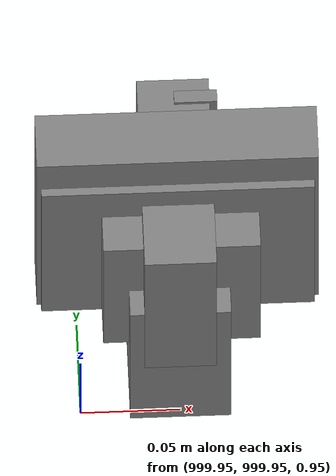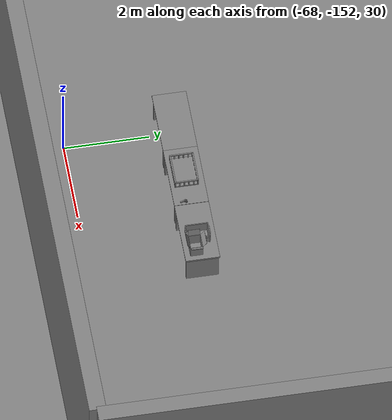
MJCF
<mujoco>
    <option gravity="0.000000000 0.000000000 -9.810000420" timestep="0.0049999999" integrator="implicitfast" density="1.225" viscosity="1.8000001e-05" noslip_iterations="10" iterations="100" sdf_iterations="50">
        <flag multiccd="disable"/>
    </option>
    <size memory="1000M"/>
    <compiler coordinate="local"/>
    <worldbody>
        <light cutoff="30" pos="0 1 1" dir="0 -1 -2"/>
        <light cutoff="30" pos="0 -1 1" dir="0 1 -2"/>
        <body pos="1000.000000000 1000.000000000 1.000000000" euler="0.000000000 0.000000000 180.000000000" name="openloong_gripper_2f85_fix_base_usda_cpu_fan">
            <geom contype="1" conaffinity="1" density="1000" type="box" material="" rgba="0.500000000 0.500000000 0.500000000 1.000000000" solimp="0.899999976 0.949999988 0.001000000" friction="1.000000000 0.005000000 0.000100000" solref="0.020000000 1.000000000" margin="0" condim="3" group="0" pos="0.000000000 0.000000000 0.070034981" quat="0.000000000 0.000000000 0.000000000 1.000000000" size="0.070700005 0.014699999 0.070700005" name="openloong_gripper_2f85_fix_base_usda_geom_5781958A_AC88_4035_88AD_47DEDFA94A26"/>
            <freejoint name="openloong_gripper_2f85_fix_base_usda_cpu_fan_joint"/>
            <site size="0.005000000 0.005000000 0.005000000" rgba="0.500000000 0.500000000 0.500000000 1.000000000" pos="0.000000000 0.000000000 0.000000000" quat="0.999961913 0.008726535 0.000000000 0.000000000" group="0" type="sphere" name="openloong_gripper_2f85_fix_base_usda_cpu_fancsite"/>
        </body>
        <body pos="1000.000000000 1000.000000000 1.000000000" euler="0.000000000 0.000000000 180.000000000" name="openloong_gripper_2f85_fix_base_usda_wifi_box">
            <geom contype="1" conaffinity="1" density="1000" type="box" material="" rgba="0.500000000 0.500000000 0.500000000 1.000000000" solimp="0.899999976 0.949999988 0.001000000" friction="1.000000000 0.005000000 0.000100000" solref="0.020000000 1.000000000" margin="0" condim="3" group="0" pos="0.000000000 0.000000000 0.058978677" quat="0.000000000 0.000000047 0.000000000 1.000000000" size="0.068499997 0.018999999 0.059000000" name="openloong_gripper_2f85_fix_base_usda_geom_EF4AA936_04A6_41CF_ADD4_9EC943F4F90B"/>
            <freejoint name="openloong_gripper_2f85_fix_base_usda_wifi_box_joint"/>
            <site size="0.005000000 0.005000000 0.005000000" rgba="0.500000000 0.500000000 0.500000000 1.000000000" pos="0.000000000 0.000000000 0.000000000" quat="0.999961913 0.008726500 0.000000000 0.000000000" group="0" type="sphere" name="openloong_gripper_2f85_fix_base_usda_wifi_boxsite"/>
        </body>
        <body pos="1000.000000000 1000.000000000 1.000000000" euler="0.000000000 0.000000000 180.000000000" name="openloong_gripper_2f85_fix_base_usda_battery_01">
            <geom contype="1" conaffinity="1" density="1000" type="box" material="" rgba="0.500000000 0.500000000 0.500000000 1.000000000" solimp="0.899999976 0.949999988 0.001000000" friction="1.000000000 0.005000000 0.000100000" solref="0.020000000 1.000000000" margin="0" condim="3" group="0" pos="-0.011123657 -0.041940309 0.101691343" quat="1.000000000 0.000000000 0.000000000 0.000000000" size="0.010800000 0.003375000 0.004725000" name="openloong_gripper_2f85_fix_base_usda_geom_B33A11E4_9DF0_437D_8528_350C69E8DD5F"/>
            <geom contype="1" conaffinity="1" density="1000" type="box" material="" rgba="0.500000000 0.500000000 0.500000000 1.000000000" solimp="0.899999976 0.949999988 0.001000000" friction="1.000000000 0.005000000 0.000100000" solref="0.020000000 1.000000000" margin="0" condim="3" group="0" pos="-0.010876465 -0.044247437 0.047066893" quat="0.998702705 -0.050920475 0.000000000 0.000000000" size="0.009450001 0.002700000 0.024975000" name="openloong_gripper_2f85_fix_base_usda_geom_366BEAEC_5E14_4BB5_B333_A947E3EB464F"/>
            <geom contype="1" conaffinity="1" density="1000" type="box" material="" rgba="0.500000000 0.500000000 0.500000000 1.000000000" solimp="0.899999976 0.949999988 0.001000000" friction="1.000000000 0.005000000 0.000100000" solref="0.020000000 1.000000000" margin="0" condim="3" group="0" pos="-0.001235962 -0.000659180 0.047381196" quat="1.000000000 0.000000000 0.000000000 0.000000000" size="0.039420001 0.039150000 0.047250003" name="openloong_gripper_2f85_fix_base_usda_geom_1DDB2D34_8029_4DA3_A9C3_0884DA9635BD"/>
            <geom contype="1" conaffinity="1" density="1000" type="box" material="" rgba="0.500000000 0.500000000 0.500000000 1.000000000" solimp="0.899999976 0.949999988 0.001000000" friction="1.000000000 0.005000000 0.000100000" solref="0.020000000 1.000000000" margin="0" condim="3" group="0" pos="-0.010876465 -0.039138794 0.009851727" quat="1.000000000 0.000000000 0.000000000 0.000000000" size="0.009450001 0.010800000 0.013500000" name="openloong_gripper_2f85_fix_base_usda_geom_7A4CF1F8_189D_4ABD_ABAE_21A98E5D4220"/>
            <geom contype="1" conaffinity="1" density="1000" type="box" material="" rgba="0.500000000 0.500000000 0.500000000 1.000000000" solimp="0.899999976 0.949999988 0.001000000" friction="1.000000000 0.005000000 0.000100000" solref="0.020000000 1.000000000" margin="0" condim="3" group="0" pos="-0.010876465 -0.041528322 0.071508206" quat="1.000000000 0.000000000 0.000000000 0.000000000" size="0.009450001 0.002700000 0.027000001" name="openloong_gripper_2f85_fix_base_usda_geom_8AEBB927_6B46_4196_A747_17D136FDED8E"/>
            <freejoint name="openloong_gripper_2f85_fix_base_usda_battery_01_joint"/>
            <site size="0.005000000 0.005000000 0.005000000" rgba="0.500000000 0.500000000 0.500000000 1.000000000" pos="0.000000000 0.000000000 0.000000000" quat="0.999961913 0.008726500 0.000000000 0.000000000" group="0" type="sphere" name="openloong_gripper_2f85_fix_base_usda_battery_01site"/>
        </body>
        <body pos="-65.981536865 -149.210906982 31.166339874" euler="84.886596680 -62.994251251 30.635831833" mocap="true" name="spotlight3_SpotLight"/>
        <body pos="1000.000000000 1000.000000000 1.000000000" euler="0.000011953 0.000005123 -179.999984741" name="openloong_gripper_2f85_fix_base_usda_intel_box">
            <geom contype="1" conaffinity="1" density="1000" type="box" material="" rgba="0.500000000 0.500000000 0.500000000 1.000000000" solimp="0.899999976 0.949999988 0.001000000" friction="1.000000000 0.005000000 0.000100000" solref="0.020000000 1.000000000" margin="0" condim="3" group="0" pos="0.000000000 -0.000067139 0.000082284" quat="0.707106709 0.000000225 0.000000253 0.707106650" size="0.052800003 0.025300000 0.052800003" name="openloong_gripper_2f85_fix_base_usda_geom_9E21303B_3D93_4362_9A58_B8F3CD20F602"/>
            <freejoint name="openloong_gripper_2f85_fix_base_usda_intel_box_joint"/>
            <site size="0.005000000 0.005000000 0.005000000" rgba="0.500000000 0.500000000 0.500000000 1.000000000" pos="0.000000000 0.000000000 0.000000000" quat="0.999961913 0.008726500 0.000000000 0.000000000" group="0" type="sphere" name="openloong_gripper_2f85_fix_base_usda_intel_boxsite"/>
        </body>
        <body pos="-65.881431580 -149.652130127 31.168537140" euler="-134.879974365 -5.298412800 -168.048080444" mocap="true" name="spotlight5_SpotLight"/>
        <body pos="1000.000000000 999.999938965 1.000000000" euler="0.000000000 0.000000000 180.000000000" name="openloong_gripper_2f85_fix_base_usda_intelcore_i5">
            <geom contype="1" conaffinity="1" density="1000" type="box" material="" rgba="0.500000000 0.500000000 0.500000000 1.000000000" solimp="0.899999976 0.949999988 0.001000000" friction="1.000000000 0.005000000 0.000100000" solref="0.020000000 1.000000000" margin="0" condim="3" group="0" pos="0.000000000 0.000000000 0.051722717" quat="0.707106709 0.000000000 0.000000000 -0.707106769" size="0.052800000 0.018080002 0.052800000" name="openloong_gripper_2f85_fix_base_usda_geom_A467437B_85FB_4BAE_9596_2C37A91B9D9F"/>
            <freejoint name="openloong_gripper_2f85_fix_base_usda_intelcore_i5_joint"/>
            <site size="0.005000000 0.005000000 0.005000000" rgba="0.500000000 0.500000000 0.500000000 1.000000000" pos="0.000000000 0.000000000 0.000000000" quat="0.999961913 0.008726534 0.000000000 0.000000000" group="0" type="sphere" name="openloong_gripper_2f85_fix_base_usda_intelcore_i5site"/>
        </body>
        <body pos="-65.890647888 -149.579025269 31.162937164" euler="21.550073624 89.230361938 87.305282593" mocap="true" name="spotlight4_SpotLight"/>
        <body pos="-64.866622925 -149.383972168 30.183746338" euler="89.999984741 89.999946594 0.000000000" name="openloong_gripper_2f85_fix_base_usda_bluebox_01">
            <geom contype="1" conaffinity="1" density="1000" type="box" material="" rgba="0.500000000 0.500000000 0.500000000 1.000000000" solimp="0.899999976 0.949999988 0.001000000" friction="1.000000000 0.005000000 0.000100000" solref="0.020000000 1.000000000" margin="0" condim="3" group="0" pos="0.276580811 0.187225342 0.000068665" quat="0.707106948 0.000077471 0.707106352 0.000077486" size="0.100000001 0.057999998 0.010000000" name="openloong_gripper_2f85_fix_base_usda_geom_AA418D50_6942_404D_8FC5_2EFAED00A2F5"/>
            <geom contype="1" conaffinity="1" density="1000" type="box" material="" rgba="0.500000000 0.500000000 0.500000000 1.000000000" solimp="0.899999976 0.949999988 0.001000000" friction="1.000000000 0.005000000 0.000100000" solref="0.020000000 1.000000000" margin="0" condim="3" group="0" pos="0.000000000 0.002883911 0.000000000" quat="0.999999881 0.000000000 0.000000000 0.000000000" size="0.254000008 0.003000000 0.172000006" name="openloong_gripper_2f85_fix_base_usda_geom_50B3B8C0_4AF2_48F6_A8B0_E3D26A8B7F73"/>
            <geom contype="1" conaffinity="1" density="1000" type="box" material="" rgba="0.500000000 0.500000000 0.500000000 1.000000000" solimp="0.899999976 0.949999988 0.001000000" friction="1.000000000 0.005000000 0.000100000" solref="0.020000000 1.000000000" margin="0" condim="3" group="0" pos="0.000000000 0.124874115 0.173484802" quat="0.999796331 0.020176515 -0.000000015 0.000000030" size="0.259999990 0.119999997 0.007000000" name="openloong_gripper_2f85_fix_base_usda_geom_994D65FD_1D40_45D6_A933_C28EB5370BB7"/>
            <geom contype="1" conaffinity="1" density="1000" type="box" material="" rgba="0.500000000 0.500000000 0.500000000 1.000000000" solimp="0.899999976 0.949999988 0.001000000" friction="1.000000000 0.005000000 0.000100000" solref="0.020000000 1.000000000" margin="0" condim="3" group="0" pos="0.000000000 0.124874115 -0.173469543" quat="0.999796331 -0.020176545 -0.000000015 0.000000000" size="0.259999990 0.119999997 0.007000000" name="openloong_gripper_2f85_fix_base_usda_geom_AE85A2FE_64CA_4183_8097_EEA1CA108CEB"/>
            <geom contype="1" conaffinity="1" density="1000" type="box" material="" rgba="0.500000000 0.500000000 0.500000000 1.000000000" solimp="0.899999976 0.949999988 0.001000000" friction="1.000000000 0.005000000 0.000100000" solref="0.020000000 1.000000000" margin="0" condim="3" group="0" pos="0.000000000 0.214008331 0.188980103" quat="0.999912977 0.013176724 0.000000015 0.000000000" size="0.259999990 0.029999999 0.012500000" name="openloong_gripper_2f85_fix_base_usda_geom_94E271E3_FF46_4DB0_863B_F11049C6ACCE"/>
            <geom contype="1" conaffinity="1" density="1000" type="box" material="" rgba="0.500000000 0.500000000 0.500000000 1.000000000" solimp="0.899999976 0.949999988 0.001000000" friction="1.000000000 0.005000000 0.000100000" solref="0.020000000 1.000000000" margin="0" condim="3" group="0" pos="-0.258361816 0.125289917 0.001876831" quat="0.702796936 -0.020792112 0.710783124 0.020769298" size="0.189999998 0.119999997 0.009000000" name="openloong_gripper_2f85_fix_base_usda_geom_FA4A2CFB_6245_4713_A64F_D0913FB9C906"/>
            <geom contype="1" conaffinity="1" density="1000" type="box" material="" rgba="0.500000000 0.500000000 0.500000000 1.000000000" solimp="0.899999976 0.949999988 0.001000000" friction="1.000000000 0.005000000 0.000100000" solref="0.020000000 1.000000000" margin="0" condim="3" group="0" pos="0.000000000 0.214008331 -0.188980103" quat="0.999912977 -0.013176769 0.000000030 0.000000015" size="0.259999990 0.029999999 0.012500000" name="openloong_gripper_2f85_fix_base_usda_geom_3E0907CE_E6D3_4CDA_B69A_9897DF3B4757"/>
            <geom contype="1" conaffinity="1" density="1000" type="box" material="" rgba="0.500000000 0.500000000 0.500000000 1.000000000" solimp="0.899999976 0.949999988 0.001000000" friction="1.000000000 0.005000000 0.000100000" solref="0.020000000 1.000000000" margin="0" condim="3" group="0" pos="-0.276611328 0.187225342 0.000068665" quat="0.707106650 0.000077441 0.707106709 0.000077456" size="0.100000001 0.057999998 0.010000000" name="openloong_gripper_2f85_fix_base_usda_geom_57AE9A12_3405_41B3_9D5E_CE4E76694E14"/>
            <geom contype="1" conaffinity="1" density="1000" type="box" material="" rgba="0.500000000 0.500000000 0.500000000 1.000000000" solimp="0.899999976 0.949999988 0.001000000" friction="1.000000000 0.005000000 0.000100000" solref="0.020000000 1.000000000" margin="0" condim="3" group="0" pos="0.258331299 0.125289917 0.001876831" quat="0.702851415 0.018856421 0.710823774 -0.019329369" size="0.189999998 0.119999997 0.009000000" name="openloong_gripper_2f85_fix_base_usda_geom_7EF9BBED_25D6_4FA7_A693_278136D77C20"/>
            <freejoint name="openloong_gripper_2f85_fix_base_usda_bluebox_01_joint"/>
            <site size="0.005000000 0.005000000 0.005000000" rgba="0.500000000 0.500000000 0.500000000 1.000000000" pos="0.000000000 0.000000000 0.000000000" quat="0.999961913 0.008726534 0.000000000 0.000000000" group="0" type="sphere" name="openloong_gripper_2f85_fix_base_usda_bluebox_01site"/>
        </body>
        <body pos="-64.496299744 -149.491867065 30.235729218" euler="0.000000000 0.000000000 89.999946594" name="openloong_gripper_2f85_fix_base_usda_cardboardbox_01">
            <geom contype="1" conaffinity="1" density="1000" type="box" material="" rgba="0.500000000 0.500000000 0.500000000 1.000000000" solimp="0.899999976 0.949999988 0.001000000" friction="1.000000000 0.005000000 0.000100000" solref="0.020000000 1.000000000" margin="0" condim="3" group="0" pos="-0.003166199 -0.004086494 0.005052090" quat="1.000000000 0.000000000 0.000000000 0.000000000" size="0.142499998 0.177500010 0.005000000" name="openloong_gripper_2f85_fix_base_usda_geom_E8563420_0973_4AB8_9582_9E4BBF13D5FD"/>
            <geom contype="1" conaffinity="1" density="1000" type="box" material="" rgba="0.500000000 0.500000000 0.500000000 1.000000000" solimp="0.899999976 0.949999988 0.001000000" friction="1.000000000 0.005000000 0.000100000" solref="0.020000000 1.000000000" margin="0" condim="3" group="0" pos="-0.003166199 0.170316696 0.150570869" quat="1.000000000 0.000000000 0.000000000 0.000000000" size="0.142499998 0.005000000 0.149999991" name="openloong_gripper_2f85_fix_base_usda_geom_43C89C1A_2880_40E5_866B_7898967095DA"/>
            <geom contype="1" conaffinity="1" density="1000" type="box" material="" rgba="0.500000000 0.500000000 0.500000000 1.000000000" solimp="0.899999976 0.949999988 0.001000000" friction="1.000000000 0.005000000 0.000100000" solref="0.020000000 1.000000000" margin="0" condim="3" group="0" pos="-0.147399902 -0.005307198 0.150570869" quat="1.000000000 0.000000000 0.000000000 0.000000000" size="0.005000000 0.177500010 0.149999991" name="openloong_gripper_2f85_fix_base_usda_geom_21382A9E_B3EE_4A36_B69E_54C075E2415F"/>
            <geom contype="1" conaffinity="1" density="1000" type="box" material="" rgba="0.500000000 0.500000000 0.500000000 1.000000000" solimp="0.899999976 0.949999988 0.001000000" friction="1.000000000 0.005000000 0.000100000" solref="0.020000000 1.000000000" margin="0" condim="3" group="0" pos="0.140275955 -0.005307198 0.150570869" quat="1.000000000 0.000000000 0.000000000 0.000000000" size="0.005000000 0.177500010 0.149999991" name="openloong_gripper_2f85_fix_base_usda_geom_6465663C_F429_40E3_A8B9_6B7F1CA6C093"/>
            <geom contype="1" conaffinity="1" density="1000" type="box" material="" rgba="0.500000000 0.500000000 0.500000000 1.000000000" solimp="0.899999976 0.949999988 0.001000000" friction="1.000000000 0.005000000 0.000100000" solref="0.020000000 1.000000000" margin="0" condim="3" group="0" pos="-0.003166199 -0.181550980 0.150570869" quat="1.000000000 0.000000000 0.000000000 0.000000000" size="0.142499998 0.005000000 0.149999991" name="openloong_gripper_2f85_fix_base_usda_geom_CEBC76C6_D4A7_44D6_8844_27924009F58A"/>
            <freejoint name="openloong_gripper_2f85_fix_base_usda_cardboardbox_01_joint"/>
            <site size="0.005000000 0.005000000 0.005000000" rgba="0.500000000 0.500000000 0.500000000 1.000000000" pos="0.000000000 0.000000000 0.000000000" quat="0.999961913 0.008726535 0.000000000 0.000000000" group="0" type="sphere" name="openloong_gripper_2f85_fix_base_usda_site_E3534B04_8C39_43E7_BC68_9E5A6584FB20"/>
            <body pos="0.139160156 -0.004048347 0.301930904" euler="-179.999954224 49.383502960 179.999954224" name="openloong_gripper_2f85_fix_base_usda_A1_006">
                <geom contype="1" conaffinity="1" density="1000" type="box" material="" rgba="0.500000000 0.500000000 0.500000000 1.000000000" solimp="0.899999976 0.949999988 0.001000000" friction="1.000000000 0.005000000 0.000100000" solref="0.020000000 1.000000000" margin="0" condim="3" group="0" pos="-0.071587563 0.000009537 0.001745224" quat="0.999999881 0.000000000 0.000000000 0.000000000" size="0.071249999 0.179999992 0.002500000" name="openloong_gripper_2f85_fix_base_usda_geom_7748EC3A_63BE_4FE7_BC8E_B596B76EF3AF"/>
                <joint armature="0" stiffness="0.07" damping="0.0099999998" axis="0.000000 1.000000 0.000000" type="hinge" name="openloong_gripper_2f85_fix_base_usda_A1_006"/>
            </body>
            <body pos="-0.145902634 -0.004086494 0.301938057" euler="-180.000000000 -60.000011444 -180.000000000" name="openloong_gripper_2f85_fix_base_usda_A2_006">
                <geom contype="1" conaffinity="1" density="1000" type="box" material="" rgba="0.500000000 0.500000000 0.500000000 1.000000000" solimp="0.899999976 0.949999988 0.001000000" friction="1.000000000 0.005000000 0.000100000" solref="0.020000000 1.000000000" margin="0" condim="3" group="0" pos="0.071268082 0.000009537 0.002717972" quat="0.000002921 0.000000000 -0.000000030 0.999999881" size="0.071249999 0.179999992 0.002500000" name="openloong_gripper_2f85_fix_base_usda_geom_EF26F6C9_6F9F_4C8E_BA3C_3ED2833D99D6"/>
                <joint armature="0" stiffness="0.07" damping="0.0099999998" axis="0.000000 1.000000 0.000000" type="hinge" name="openloong_gripper_2f85_fix_base_usda_A2_006"/>
            </body>
            <body pos="-0.003385544 0.175991058 0.301930904" euler="-125.858116150 -0.000004561 0.000002331" name="openloong_gripper_2f85_fix_base_usda_B2_006">
                <geom contype="1" conaffinity="1" density="1000" type="box" material="" rgba="0.500000000 0.500000000 0.500000000 1.000000000" solimp="0.899999976 0.949999988 0.001000000" friction="1.000000000 0.005000000 0.000100000" solref="0.020000000 1.000000000" margin="0" condim="3" group="0" pos="0.000009537 -0.070939064 -0.002470016" quat="0.999614120 0.027776197 -0.000000015 0.000000030" size="0.137500003 0.064999998 0.005000000" name="openloong_gripper_2f85_fix_base_usda_geom_FC53D5F7_258C_4115_8531_E8902F1E0216"/>
                <joint armature="0" stiffness="0.07" damping="0.0099999998" axis="1.000000 0.000000 0.000000" type="hinge" name="openloong_gripper_2f85_fix_base_usda_B2_006"/>
            </body>
            <body pos="-0.003385544 -0.184140205 0.301938057" euler="147.805557251 0.000000000 0.000000000" name="openloong_gripper_2f85_fix_base_usda_B1_006">
                <geom contype="1" conaffinity="1" density="1000" type="box" material="" rgba="0.500000000 0.500000000 0.500000000 1.000000000" solimp="0.899999976 0.949999988 0.001000000" friction="1.000000000 0.005000000 0.000100000" solref="0.020000000 1.000000000" margin="0" condim="3" group="0" pos="-0.000028610 0.070202351 -0.002703667" quat="0.999614179 -0.027776167 0.000000000 0.000000000" size="0.137500003 0.064999998 0.005000000" name="openloong_gripper_2f85_fix_base_usda_geom_A481EFB8_E228_42A7_9F41_A6FBAF97F945"/>
                <joint armature="0" stiffness="0.07" damping="0.0099999998" axis="1.000000 0.000000 0.000000" type="hinge" name="openloong_gripper_2f85_fix_base_usda_B1_006"/>
            </body>
        </body>
        <body pos="-65.882858276 -149.481979370 30.229999542" euler="-64.487716675 0.000000000 0.000000000" name="openloong_gripper_2f85_fix_base_usda_Barcode">
            <geom contype="1" conaffinity="1" density="1000" type="box" material="" rgba="0.500000000 0.500000000 0.500000000 1.000000000" solimp="0.899999976 0.949999988 0.001000000" friction="1.000000000 0.005000000 0.000100000" solref="0.020000000 1.000000000" margin="0" condim="3" group="0" pos="0.000000000 0.013038635 0.001419067" quat="0.000000000 0.000000000 0.000000000 1.000000119" size="0.034000002 0.010000000 0.017999999" name="openloong_gripper_2f85_fix_base_usda_geom_478BEFE6_E070_484C_9729_646E63B4AC8C"/>
            <geom contype="1" conaffinity="1" density="1000" type="box" material="" rgba="0.500000000 0.500000000 0.500000000 1.000000000" solimp="0.899999976 0.949999988 0.001000000" friction="1.000000000 0.005000000 0.000100000" solref="0.020000000 1.000000000" margin="0" condim="3" group="0" pos="0.000000000 -0.035301208 -0.007095337" quat="0.000000000 0.000000000 -0.043619365 0.999048233" size="0.028999999 0.010000000 0.020000000" name="openloong_gripper_2f85_fix_base_usda_geom_88256085_F275_4D9A_BF06_397772AE08DF"/>
            <geom contype="1" conaffinity="1" density="1000" type="box" material="" rgba="0.500000000 0.500000000 0.500000000 1.000000000" solimp="0.899999976 0.949999988 0.001000000" friction="1.000000000 0.005000000 0.000100000" solref="0.020000000 1.000000000" margin="0" condim="3" group="0" pos="0.000000000 -0.043411255 -0.011749268" quat="0.922262907 0.386563420 0.000000000 0.000000000" size="0.026000001 0.010000000 0.020000000" name="openloong_gripper_2f85_fix_base_usda_geom_345F821A_ABFF_46A0_A6BC_CC377BC5FB59"/>
            <geom contype="1" conaffinity="1" density="1000" type="box" material="" rgba="0.500000000 0.500000000 0.500000000 1.000000000" solimp="0.899999976 0.949999988 0.001000000" friction="1.000000000 0.005000000 0.000100000" solref="0.020000000 1.000000000" margin="0" condim="3" group="0" pos="0.000000000 -0.016967773 -0.031860352" quat="0.000000000 0.000000000 0.000000000 1.000000119" size="0.008000000 0.010000000 0.013000000" name="openloong_gripper_2f85_fix_base_usda_geom_74F8DD62_B5FF_44A7_9BDE_02C847BB6874"/>
            <geom contype="1" conaffinity="1" density="1000" type="box" material="" rgba="0.500000000 0.500000000 0.500000000 1.000000000" solimp="0.899999976 0.949999988 0.001000000" friction="1.000000000 0.005000000 0.000100000" solref="0.020000000 1.000000000" margin="0" condim="3" group="0" pos="0.000000000 -0.001869202 0.000312805" quat="0.953716993 0.300705761 0.000000000 0.000000000" size="0.032000002 0.010000000 0.018999999" name="openloong_gripper_2f85_fix_base_usda_geom_EB83F61D_E8F1_4848_BEF9_E87362A446B2"/>
            <geom contype="1" conaffinity="1" density="1000" type="box" material="" rgba="0.500000000 0.500000000 0.500000000 1.000000000" solimp="0.899999976 0.949999988 0.001000000" friction="1.000000000 0.005000000 0.000100000" solref="0.020000000 1.000000000" margin="0" condim="3" group="0" pos="0.000000000 -0.019531250 -0.003173828" quat="0.953716993 0.300705761 0.000000000 0.000000000" size="0.030999999 0.010000000 0.020000000" name="openloong_gripper_2f85_fix_base_usda_geom_330BDBC4_5467_4254_A5BE_949DA483B715"/>
            <geom contype="1" conaffinity="1" density="1000" type="box" material="" rgba="0.500000000 0.500000000 0.500000000 1.000000000" solimp="0.899999976 0.949999988 0.001000000" friction="1.000000000 0.005000000 0.000100000" solref="0.020000000 1.000000000" margin="0" condim="3" group="0" pos="0.000000000 -0.035301208 -0.007095337" quat="0.953716993 0.300705761 0.000000000 0.000000000" size="0.028999999 0.010000000 0.020000000" name="openloong_gripper_2f85_fix_base_usda_geom_8DABB313_D91B_46EA_BD11_28982FAE37BF"/>
            <geom contype="1" conaffinity="1" density="1000" type="box" material="" rgba="0.500000000 0.500000000 0.500000000 1.000000000" solimp="0.899999976 0.949999988 0.001000000" friction="1.000000000 0.005000000 0.000100000" solref="0.020000000 1.000000000" margin="0" condim="3" group="0" pos="0.000000000 -0.042617798 -0.071121216" quat="0.000000000 0.000000000 0.000000000 1.000000119" size="0.013000000 0.021000000 0.059999999" name="openloong_gripper_2f85_fix_base_usda_geom_07FCBDF3_02A0_48C0_B580_ECC701548B44"/>
            <freejoint name="openloong_gripper_2f85_fix_base_usda_Barcode_joint"/>
            <site size="0.005000000 0.005000000 0.005000000" rgba="0.500000000 0.500000000 0.500000000 1.000000000" pos="0.000000000 0.000000000 0.000000000" quat="1.000000000 0.000000000 0.000000000 0.000000000" group="0" type="sphere" name="openloong_gripper_2f85_fix_base_usda_Barcode_site"/>
        </body>
        <body pos="-66.745018005 -149.392349243 30.184000015" euler="0.000000000 0.000000000 89.999946594" name="[22332551448623]_Basket_01">
            <geom contype="1" conaffinity="1" density="1000" type="box" material="" rgba="0.500000000 0.500000000 0.500000000 1.000000000" solimp="0.899999976 0.949999988 0.001000000" friction="1.000000000 0.005000000 0.000100000" solref="0.020000000 1.000000000" margin="0" condim="3" group="0" pos="-0.052425385 0.389207840 0.089787483" quat="0.707107008 0.000000000 0.000000000 0.707106411" size="0.014249999 0.014249999 0.059999999" name="[22332551448623]_geom_BE41DF28_C77E_4EF6_ABE8_98FDCE2937C2"/>
            <geom contype="1" conaffinity="1" density="1000" type="box" material="" rgba="0.500000000 0.500000000 0.500000000 1.000000000" solimp="0.899999976 0.949999988 0.001000000" friction="1.000000000 0.005000000 0.000100000" solref="0.020000000 1.000000000" margin="0" condim="3" group="0" pos="0.264015198 -0.133043289 0.089787483" quat="0.707107008 0.000000000 0.000000000 0.707106411" size="0.014249999 0.014249999 0.059999999" name="[22332551448623]_geom_03730351_1CE8_4B2F_B8BE_1C31FE295A93"/>
            <geom contype="1" conaffinity="1" density="1000" type="box" material="" rgba="0.500000000 0.500000000 0.500000000 1.000000000" solimp="0.899999976 0.949999988 0.001000000" friction="1.000000000 0.005000000 0.000100000" solref="0.020000000 1.000000000" margin="0" condim="3" group="0" pos="-0.264015198 -0.265548706 0.089793205" quat="0.707107008 0.000000000 0.000000000 0.707106411" size="0.014249999 0.014249999 0.059999999" name="[22332551448623]_geom_0C1D4A71_AA27_4147_BCE8_DB7FFAB41829"/>
            <geom contype="1" conaffinity="1" density="1000" type="box" material="" rgba="0.500000000 0.500000000 0.500000000 1.000000000" solimp="0.899999976 0.949999988 0.001000000" friction="1.000000000 0.005000000 0.000100000" solref="0.020000000 1.000000000" margin="0" condim="3" group="0" pos="-0.160263062 -0.389322281 0.089793205" quat="0.707107008 0.000000000 0.000000000 0.707106411" size="0.014249999 0.014249999 0.059999999" name="[22332551448623]_geom_E07DD9DF_764E_42C8_BAC1_B813DB6DC34C"/>
            <geom contype="1" conaffinity="1" density="1000" type="box" material="" rgba="0.500000000 0.500000000 0.500000000 1.000000000" solimp="0.899999976 0.949999988 0.001000000" friction="1.000000000 0.005000000 0.000100000" solref="0.020000000 1.000000000" margin="0" condim="3" group="0" pos="0.162265778 -0.389322281 0.089787483" quat="0.707107008 0.000000000 0.000000000 0.707106411" size="0.014249999 0.014249999 0.059999999" name="[22332551448623]_geom_BCB1A6EC_D57C_4FB1_A3DC_94185E96A390"/>
            <geom contype="1" conaffinity="1" density="1000" type="box" material="" rgba="0.500000000 0.500000000 0.500000000 1.000000000" solimp="0.899999976 0.949999988 0.001000000" friction="1.000000000 0.005000000 0.000100000" solref="0.020000000 1.000000000" margin="0" condim="3" group="0" pos="0.264015198 0.389207840 0.089787483" quat="0.707107008 0.000000000 0.000000000 0.707106411" size="0.014249999 0.014249999 0.059999999" name="[22332551448623]_geom_9D0C6BF4_E9A5_4A11_9FB6_D4AE453C2C19"/>
            <geom contype="1" conaffinity="1" density="1000" type="box" material="" rgba="0.500000000 0.500000000 0.500000000 1.000000000" solimp="0.899999976 0.949999988 0.001000000" friction="1.000000000 0.005000000 0.000100000" solref="0.020000000 1.000000000" margin="0" condim="3" group="0" pos="-0.264015198 -0.133043289 0.089793205" quat="0.707107008 0.000000000 0.000000000 0.707106411" size="0.014249999 0.014249999 0.059999999" name="[22332551448623]_geom_2E204D20_5CF3_4AB0_9F4A_927E985B7649"/>
            <geom contype="1" conaffinity="1" density="1000" type="box" material="" rgba="0.500000000 0.500000000 0.500000000 1.000000000" solimp="0.899999976 0.949999988 0.001000000" friction="1.000000000 0.005000000 0.000100000" solref="0.020000000 1.000000000" margin="0" condim="3" group="0" pos="-0.264026642 0.269256592 0.089793205" quat="0.707107008 0.000000000 0.000000000 0.707106411" size="0.014249999 0.014249999 0.059999999" name="[22332551448623]_geom_F5B488DE_39C5_4102_A28F_37C159A35D1C"/>
            <geom contype="1" conaffinity="1" density="1000" type="box" material="" rgba="0.500000000 0.500000000 0.500000000 1.000000000" solimp="0.899999976 0.949999988 0.001000000" friction="1.000000000 0.005000000 0.000100000" solref="0.020000000 1.000000000" margin="0" condim="3" group="0" pos="0.054462433 0.389207840 0.089787483" quat="0.707107008 0.000000000 0.000000000 0.707106411" size="0.014249999 0.014249999 0.059999999" name="[22332551448623]_geom_EE2245E6_BDEF_4488_A49A_BE1C2EAB43AE"/>
            <geom contype="1" conaffinity="1" density="1000" type="box" material="" rgba="0.500000000 0.500000000 0.500000000 1.000000000" solimp="0.899999976 0.949999988 0.001000000" friction="1.000000000 0.005000000 0.000100000" solref="0.020000000 1.000000000" margin="0" condim="3" group="0" pos="0.054462433 -0.389322281 0.089787483" quat="0.707107008 0.000000000 0.000000000 0.707106411" size="0.014249999 0.014249999 0.059999999" name="[22332551448623]_geom_4329EF59_494F_493E_ADD4_7114B3BB2C83"/>
            <geom contype="1" conaffinity="1" density="1000" type="box" material="" rgba="0.500000000 0.500000000 0.500000000 1.000000000" solimp="0.899999976 0.949999988 0.001000000" friction="1.000000000 0.005000000 0.000100000" solref="0.020000000 1.000000000" margin="0" condim="3" group="0" pos="0.264015198 0.269256592 0.089793205" quat="0.707107008 0.000000000 0.000000000 0.707106411" size="0.014249999 0.014249999 0.059999999" name="[22332551448623]_geom_3EC418FE_542B_4882_B5D4_9205E876A2D0"/>
            <geom contype="1" conaffinity="1" density="1000" type="box" material="" rgba="0.500000000 0.500000000 0.500000000 1.000000000" solimp="0.899999976 0.949999988 0.001000000" friction="1.000000000 0.005000000 0.000100000" solref="0.020000000 1.000000000" margin="0" condim="3" group="0" pos="0.264015198 -0.389322281 0.089787483" quat="0.707107008 0.000000000 0.000000000 0.707106411" size="0.014249999 0.014249999 0.059999999" name="[22332551448623]_geom_5851C6CB_7840_4E7A_BF2E_3F2DDE85D82F"/>
            <geom contype="1" conaffinity="1" density="1000" type="box" material="" rgba="0.500000000 0.500000000 0.500000000 1.000000000" solimp="0.899999976 0.949999988 0.001000000" friction="1.000000000 0.005000000 0.000100000" solref="0.020000000 1.000000000" margin="0" condim="3" group="0" pos="0.000000000 0.000000000 0.015998840" quat="0.707107008 0.000000000 0.000000000 0.707106411" size="0.403499991 0.279000014 0.015750000" name="[22332551448623]_geom_0910A7F9_904F_4568_8327_0003673CA513"/>
            <geom contype="1" conaffinity="1" density="1000" type="box" material="" rgba="0.500000000 0.500000000 0.500000000 1.000000000" solimp="0.899999976 0.949999988 0.001000000" friction="1.000000000 0.005000000 0.000100000" solref="0.020000000 1.000000000" margin="0" condim="3" group="0" pos="0.000000000 -0.389476776 0.163619041" quat="0.707107008 0.000000000 0.000000000 0.707106411" size="0.015000000 0.277500004 0.015750000" name="[22332551448623]_geom_F0B61B60_8426_48E4_BE49_22F6B2D22CE8"/>
            <geom contype="1" conaffinity="1" density="1000" type="box" material="" rgba="0.500000000 0.500000000 0.500000000 1.000000000" solimp="0.899999976 0.949999988 0.001000000" friction="1.000000000 0.005000000 0.000100000" solref="0.020000000 1.000000000" margin="0" condim="3" group="0" pos="0.162265778 0.389207840 0.089787483" quat="0.707107008 0.000000000 0.000000000 0.707106411" size="0.014249999 0.014249999 0.059999999" name="[22332551448623]_geom_0D640CB1_C0B9_411E_A1EB_976D08F611A4"/>
            <geom contype="1" conaffinity="1" density="1000" type="box" material="" rgba="0.500000000 0.500000000 0.500000000 1.000000000" solimp="0.899999976 0.949999988 0.001000000" friction="1.000000000 0.005000000 0.000100000" solref="0.020000000 1.000000000" margin="0" condim="3" group="0" pos="0.000000000 0.389471054 0.163619041" quat="0.707107008 0.000000000 0.000000000 0.707106411" size="0.015000000 0.277500004 0.015750000" name="[22332551448623]_geom_0BD7B4B8_748E_4FE9_8AED_7A3660A36A61"/>
            <geom contype="1" conaffinity="1" density="1000" type="box" material="" rgba="0.500000000 0.500000000 0.500000000 1.000000000" solimp="0.899999976 0.949999988 0.001000000" friction="1.000000000 0.005000000 0.000100000" solref="0.020000000 1.000000000" margin="0" condim="3" group="0" pos="-0.263511658 0.000000000 0.163619041" quat="0.707107008 0.000000000 0.000000000 0.707106411" size="0.403499991 0.015000000 0.015750000" name="[22332551448623]_geom_073171F5_B6CF_4ADF_B434_1D918A7BD5F3"/>
            <geom contype="1" conaffinity="1" density="1000" type="box" material="" rgba="0.500000000 0.500000000 0.500000000 1.000000000" solimp="0.899999976 0.949999988 0.001000000" friction="1.000000000 0.005000000 0.000100000" solref="0.020000000 1.000000000" margin="0" condim="3" group="0" pos="-0.264015198 0.141334534 0.089793205" quat="0.707107008 0.000000000 0.000000000 0.707106411" size="0.014249999 0.014249999 0.059999999" name="[22332551448623]_geom_F580AA73_6DB3_4FF3_A8D2_132840C6CF09"/>
            <geom contype="1" conaffinity="1" density="1000" type="box" material="" rgba="0.500000000 0.500000000 0.500000000 1.000000000" solimp="0.899999976 0.949999988 0.001000000" friction="1.000000000 0.005000000 0.000100000" solref="0.020000000 1.000000000" margin="0" condim="3" group="0" pos="0.264015198 -0.265548706 0.089787483" quat="0.707107008 0.000000000 0.000000000 0.707106411" size="0.014249999 0.014249999 0.059999999" name="[22332551448623]_geom_CEFBAC38_B858_49CB_976D_46EAAF8D97F2"/>
            <geom contype="1" conaffinity="1" density="1000" type="box" material="" rgba="0.500000000 0.500000000 0.500000000 1.000000000" solimp="0.899999976 0.949999988 0.001000000" friction="1.000000000 0.005000000 0.000100000" solref="0.020000000 1.000000000" margin="0" condim="3" group="0" pos="-0.160263062 0.389207840 0.089787483" quat="0.707107008 0.000000000 0.000000000 0.707106411" size="0.014249999 0.014249999 0.059999999" name="[22332551448623]_geom_E6E5D4CE_D6A3_4BAA_9A1F_1E4B51021305"/>
            <geom contype="1" conaffinity="1" density="1000" type="box" material="" rgba="0.500000000 0.500000000 0.500000000 1.000000000" solimp="0.899999976 0.949999988 0.001000000" friction="1.000000000 0.005000000 0.000100000" solref="0.020000000 1.000000000" margin="0" condim="3" group="0" pos="-0.052425385 -0.389322281 0.089787483" quat="0.707107008 0.000000000 0.000000000 0.707106411" size="0.014249999 0.014249999 0.059999999" name="[22332551448623]_geom_A46F1F9D_3ECD_4E08_B7CC_94365697A9C5"/>
            <geom contype="1" conaffinity="1" density="1000" type="box" material="" rgba="0.500000000 0.500000000 0.500000000 1.000000000" solimp="0.899999976 0.949999988 0.001000000" friction="1.000000000 0.005000000 0.000100000" solref="0.020000000 1.000000000" margin="0" condim="3" group="0" pos="-0.264026642 -0.389322281 0.089793205" quat="0.707107008 0.000000000 0.000000000 0.707106411" size="0.014249999 0.014249999 0.059999999" name="[22332551448623]_geom_AAC33B46_C8D7_4DE4_80A2_3FFB5B605D95"/>
            <geom contype="1" conaffinity="1" density="1000" type="box" material="" rgba="0.500000000 0.500000000 0.500000000 1.000000000" solimp="0.899999976 0.949999988 0.001000000" friction="1.000000000 0.005000000 0.000100000" solref="0.020000000 1.000000000" margin="0" condim="3" group="0" pos="0.264015198 0.141334534 0.089787483" quat="0.707107008 0.000000000 0.000000000 0.707106411" size="0.014249999 0.014249999 0.059999999" name="[22332551448623]_geom_A96853E9_1DEC_40A8_B1CA_EABB30878C58"/>
            <geom contype="1" conaffinity="1" density="1000" type="box" material="" rgba="0.500000000 0.500000000 0.500000000 1.000000000" solimp="0.899999976 0.949999988 0.001000000" friction="1.000000000 0.005000000 0.000100000" solref="0.020000000 1.000000000" margin="0" condim="3" group="0" pos="-0.264015198 0.389207840 0.089793205" quat="0.707107008 0.000000000 0.000000000 0.707106411" size="0.014249999 0.014249999 0.059999999" name="[22332551448623]_geom_A3DEFEF5_5054_4DE0_9190_6A2B30C5DEA2"/>
            <geom contype="1" conaffinity="1" density="1000" type="box" material="" rgba="0.500000000 0.500000000 0.500000000 1.000000000" solimp="0.899999976 0.949999988 0.001000000" friction="1.000000000 0.005000000 0.000100000" solref="0.020000000 1.000000000" margin="0" condim="3" group="0" pos="0.264015198 0.004480362 0.089787483" quat="0.707107008 0.000000000 0.000000000 0.707106411" size="0.014249999 0.014249999 0.059999999" name="[22332551448623]_geom_48239D4C_3B37_42EC_A7F0_CD5F409B07B4"/>
            <geom contype="1" conaffinity="1" density="1000" type="box" material="" rgba="0.500000000 0.500000000 0.500000000 1.000000000" solimp="0.899999976 0.949999988 0.001000000" friction="1.000000000 0.005000000 0.000100000" solref="0.020000000 1.000000000" margin="0" condim="3" group="0" pos="0.263694763 -0.000011444 0.163619041" quat="0.707107008 0.000000000 0.000000000 0.707106411" size="0.403499991 0.015000000 0.015750000" name="[22332551448623]_geom_A5713843_5232_49CA_93D8_172E8E4C2519"/>
            <geom contype="1" conaffinity="1" density="1000" type="box" material="" rgba="0.500000000 0.500000000 0.500000000 1.000000000" solimp="0.899999976 0.949999988 0.001000000" friction="1.000000000 0.005000000 0.000100000" solref="0.020000000 1.000000000" margin="0" condim="3" group="0" pos="-0.264015198 0.004480362 0.089793205" quat="0.707107008 0.000000000 0.000000000 0.707106411" size="0.014249999 0.014249999 0.059999999" name="[22332551448623]_geom_C4D527F8_3D6F_485B_A218_3C40BC55DAFF"/>
            <freejoint name="[22332551448623]_joint_CE4CFC79_0C62_4DB3_A27D_62547D626AD5"/>
        </body>
        <body pos="0.000000000 0.000000000 0.000000000" euler="0.000000000 0.000000000 0.000000000" name="Static Objects_Static Objects">
            <geom contype="1" conaffinity="1" density="1000" type="box" material="" rgba="0.500000000 0.500000000 0.500000000 1.000000000" solimp="0.899999976 0.949999988 0.001000000" friction="1.000000000 0.005000000 0.000100000" solref="0.020000000 1.000000000" margin="0" condim="3" group="0" pos="-67.544113159 -149.365814209 29.727830887" quat="0.500000417 0.499999970 0.499999553 0.499999970" size="0.381000012 0.319999993 0.041000001" name="Static Objects_geom_DE9E5770_5267_4186_87FA_51293F667453"/>
            <geom contype="1" conaffinity="1" density="1000" type="box" material="" rgba="0.500000000 0.500000000 0.500000000 1.000000000" solimp="0.899999976 0.949999988 0.001000000" friction="1.000000000 0.005000000 0.000100000" solref="0.020000000 1.000000000" margin="0" condim="3" group="0" pos="-68.239501953 -149.365814209 30.086868286" quat="0.500000417 0.499999970 0.499999553 0.499999970" size="0.370999992 0.039500002 0.745000005" name="Static Objects_geom_94C1306E_38CA_4FE9_8A0E_3735229E8255"/>
            <geom contype="1" conaffinity="1" density="1000" type="box" material="" rgba="0.500000000 0.500000000 0.500000000 1.000000000" solimp="0.899999976 0.949999988 0.001000000" friction="1.000000000 0.005000000 0.000100000" solref="0.020000000 1.000000000" margin="0" condim="3" group="0" pos="-68.239501953 -149.365814209 30.147235870" quat="0.500000417 0.499999970 0.499999553 0.499999970" size="0.400000006 0.022000000 0.800000012" name="Static Objects_geom_65C2D09B_C175_414A_9C3F_7132A685295B"/>
            <geom contype="1" conaffinity="1" density="1000" type="box" material="" rgba="0.500000000 0.500000000 0.500000000 1.000000000" solimp="0.899999976 0.949999988 0.001000000" friction="1.000000000 0.005000000 0.000100000" solref="0.020000000 1.000000000" margin="0" condim="3" group="0" pos="-68.934890747 -149.365814209 29.727830887" quat="0.500000417 0.499999970 0.499999553 0.499999970" size="0.381000012 0.319999993 0.041000001" name="Static Objects_geom_35EA6203_5D92_4267_81D9_C6ECD966B225"/>
            <geom contype="1" conaffinity="1" density="1000" type="box" material="" rgba="0.500000000 0.500000000 0.500000000 1.000000000" solimp="0.899999976 0.949999988 0.001000000" friction="1.000000000 0.005000000 0.000100000" solref="0.020000000 1.000000000" margin="0" condim="3" group="0" pos="-68.239501953 -149.365814209 29.561563492" quat="0.500000417 0.499999970 0.499999553 0.499999970" size="0.020000000 0.022000000 0.660000026" name="Static Objects_geom_256DA9D5_4CF9_403B_B6E2_BC1ACEDC22F1"/>
            <geom contype="1" conaffinity="1" density="1000" type="box" material="" rgba="0.500000000 0.500000000 0.500000000 1.000000000" solimp="0.899999976 0.949999988 0.001000000" friction="1.000000000 0.005000000 0.000100000" solref="0.020000000 1.000000000" margin="0" condim="3" group="0" pos="-65.945671082 -149.365814209 29.727830887" quat="0.500000417 0.499999970 0.499999553 0.499999970" size="0.381000012 0.319999993 0.041000001" name="Static Objects_geom_3F08AE32_7243_409A_9731_45DC92E04EAC"/>
            <geom contype="1" conaffinity="1" density="1000" type="box" material="" rgba="0.500000000 0.500000000 0.500000000 1.000000000" solimp="0.899999976 0.949999988 0.001000000" friction="1.000000000 0.005000000 0.000100000" solref="0.020000000 1.000000000" margin="0" condim="3" group="0" pos="-66.641059875 -149.365814209 30.086868286" quat="0.500000417 0.499999970 0.499999553 0.499999970" size="0.370999992 0.039500002 0.745000005" name="Static Objects_geom_84A8D9AB_3413_4562_92CD_271107E1328F"/>
            <geom contype="1" conaffinity="1" density="1000" type="box" material="" rgba="0.500000000 0.500000000 0.500000000 1.000000000" solimp="0.899999976 0.949999988 0.001000000" friction="1.000000000 0.005000000 0.000100000" solref="0.020000000 1.000000000" margin="0" condim="3" group="0" pos="-66.641059875 -149.365814209 30.147235870" quat="0.500000417 0.499999970 0.499999553 0.499999970" size="0.400000006 0.022000000 0.800000012" name="Static Objects_geom_B69D96CD_DB45_4266_88F8_CBFB277B966E"/>
            <geom contype="1" conaffinity="1" density="1000" type="box" material="" rgba="0.500000000 0.500000000 0.500000000 1.000000000" solimp="0.899999976 0.949999988 0.001000000" friction="1.000000000 0.005000000 0.000100000" solref="0.020000000 1.000000000" margin="0" condim="3" group="0" pos="-67.336448669 -149.365814209 29.727830887" quat="0.500000417 0.499999970 0.499999553 0.499999970" size="0.381000012 0.319999993 0.041000001" name="Static Objects_geom_1FBF8183_CAE9_40B2_AB0F_BBAF0F492605"/>
            <geom contype="1" conaffinity="1" density="1000" type="box" material="" rgba="0.500000000 0.500000000 0.500000000 1.000000000" solimp="0.899999976 0.949999988 0.001000000" friction="1.000000000 0.005000000 0.000100000" solref="0.020000000 1.000000000" margin="0" condim="3" group="0" pos="-66.641059875 -149.365814209 29.561563492" quat="0.500000417 0.499999970 0.499999553 0.499999970" size="0.020000000 0.022000000 0.660000026" name="Static Objects_geom_CFB8F86D_B98E_465E_8F16_9FEE341DA358"/>
            <geom contype="1" conaffinity="1" density="1000" type="box" material="" rgba="0.500000000 0.500000000 0.500000000 1.000000000" solimp="0.899999976 0.949999988 0.001000000" friction="1.000000000 0.005000000 0.000100000" solref="0.020000000 1.000000000" margin="0" condim="3" group="0" pos="-64.338577271 -149.365814209 29.727830887" quat="0.500000417 0.499999970 0.499999553 0.499999970" size="0.381000012 0.319999993 0.041000001" name="Static Objects_geom_8C083240_B907_4C5F_B723_A88A64DE46ED"/>
            <geom contype="1" conaffinity="1" density="1000" type="box" material="" rgba="0.500000000 0.500000000 0.500000000 1.000000000" solimp="0.899999976 0.949999988 0.001000000" friction="1.000000000 0.005000000 0.000100000" solref="0.020000000 1.000000000" margin="0" condim="3" group="0" pos="-65.033966064 -149.365814209 30.086868286" quat="0.500000417 0.499999970 0.499999553 0.499999970" size="0.370999992 0.039500002 0.745000005" name="Static Objects_geom_FB4FC2B7_575A_4EC5_93F8_B559E68AD4E7"/>
            <geom contype="1" conaffinity="1" density="1000" type="box" material="" rgba="0.500000000 0.500000000 0.500000000 1.000000000" solimp="0.899999976 0.949999988 0.001000000" friction="1.000000000 0.005000000 0.000100000" solref="0.020000000 1.000000000" margin="0" condim="3" group="0" pos="-65.033966064 -149.365814209 30.147235870" quat="0.500000417 0.499999970 0.499999553 0.499999970" size="0.400000006 0.022000000 0.800000012" name="Static Objects_geom_2F0F2052_EDA1_4877_8CF5_9058D9FD8D01"/>
            <geom contype="1" conaffinity="1" density="1000" type="box" material="" rgba="0.500000000 0.500000000 0.500000000 1.000000000" solimp="0.899999976 0.949999988 0.001000000" friction="1.000000000 0.005000000 0.000100000" solref="0.020000000 1.000000000" margin="0" condim="3" group="0" pos="-65.729354858 -149.365814209 29.727830887" quat="0.500000417 0.499999970 0.499999553 0.499999970" size="0.381000012 0.319999993 0.041000001" name="Static Objects_geom_E497BA2E_1867_4273_A6EC_8274D2727EF4"/>
            <geom contype="1" conaffinity="1" density="1000" type="box" material="" rgba="0.500000000 0.500000000 0.500000000 1.000000000" solimp="0.899999976 0.949999988 0.001000000" friction="1.000000000 0.005000000 0.000100000" solref="0.020000000 1.000000000" margin="0" condim="3" group="0" pos="-65.033966064 -149.365814209 29.561563492" quat="0.500000417 0.499999970 0.499999553 0.499999970" size="0.020000000 0.022000000 0.660000026" name="Static Objects_geom_3809F3BB_2438_46AF_919B_5022CB3E682A"/>
            <geom contype="1" conaffinity="1" density="1000" type="box" material="" rgba="0.500000000 0.500000000 0.500000000 1.000000000" solimp="0.899999976 0.949999988 0.001000000" friction="1.000000000 0.005000000 0.000100000" solref="0.020000000 1.000000000" margin="0" condim="3" group="0" pos="-61.754566193 -137.853729248 33.906845093" quat="0.707107067 0.000000000 0.000000000 0.707106471" size="0.759999990 0.759999990 4.500000000" name="Static Objects_geom_16EA2030_1725_4984_B1C3_C25A54A71EBD"/>
            <geom contype="1" conaffinity="1" density="1000" type="box" material="" rgba="0.500000000 0.500000000 0.500000000 1.000000000" solimp="0.899999976 0.949999988 0.001000000" friction="1.000000000 0.005000000 0.000100000" solref="0.020000000 1.000000000" margin="0" condim="3" group="0" pos="-57.511135101 -144.927108765 31.707921982" quat="1.000000000 0.000000000 0.000000000 0.000000000" size="0.200000003 8.000000000 2.299999952" name="Static Objects_geom_481DEC2A_3140_4590_BF1D_EDE8B24C8B36"/>
            <geom contype="1" conaffinity="1" density="1000" type="box" material="" rgba="0.500000000 0.500000000 0.500000000 1.000000000" solimp="0.899999976 0.949999988 0.001000000" friction="1.000000000 0.005000000 0.000100000" solref="0.020000000 1.000000000" margin="0" condim="3" group="0" pos="-80.517646790 -157.574050903 31.688196182" quat="0.707107067 0.000000000 0.000000000 0.707106471" size="0.600000024 0.600000024 2.299999952" name="Static Objects_geom_C4FD7BEB_5A0A_47ED_ACE9_B117ECC28FE8"/>
            <geom contype="1" conaffinity="1" density="1000" type="box" material="" rgba="0.500000000 0.500000000 0.500000000 1.000000000" solimp="0.899999976 0.949999988 0.001000000" friction="1.000000000 0.005000000 0.000100000" solref="0.020000000 1.000000000" margin="0" condim="3" group="0" pos="-80.711044312 -147.414932251 31.666158676" quat="1.000000000 0.000000000 0.000000000 0.000000000" size="0.200000003 10.000000000 2.299999952" name="Static Objects_geom_8A7C36AB_FE3D_4707_9CED_6D55C2589FC1"/>
            <geom contype="1" conaffinity="1" density="1000" type="box" material="" rgba="0.500000000 0.500000000 0.500000000 1.000000000" solimp="0.899999976 0.949999988 0.001000000" friction="1.000000000 0.005000000 0.000100000" solref="0.020000000 1.000000000" margin="0" condim="3" group="0" pos="-57.687217712 -137.434692383 31.688196182" quat="0.707107067 0.000000000 0.000000000 0.707106471" size="0.600000024 0.600000024 2.299999952" name="Static Objects_geom_D7E3B086_5055_4D9E_B691_F3814BB58136"/>
            <geom contype="1" conaffinity="1" density="1000" type="box" material="" rgba="0.500000000 0.500000000 0.500000000 1.000000000" solimp="0.899999976 0.949999988 0.001000000" friction="1.000000000 0.005000000 0.000100000" solref="0.020000000 1.000000000" margin="0" condim="3" group="0" pos="-69.537033081 -140.263229370 31.714921951" quat="0.707107067 0.000000000 0.000000000 0.707106471" size="0.759999990 4.500000000 2.299999952" name="Static Objects_geom_2A9402BF_17BE_4BED_BEF6_80E5E905F3C5"/>
            <geom contype="1" conaffinity="1" density="1000" type="box" material="" rgba="0.500000000 0.500000000 0.500000000 1.000000000" solimp="0.899999976 0.949999988 0.001000000" friction="1.000000000 0.005000000 0.000100000" solref="0.020000000 1.000000000" margin="0" condim="3" group="0" pos="-80.073638916 -137.853713989 33.906845093" quat="0.707107067 0.000000000 0.000000000 0.707106471" size="0.759999990 0.759999990 4.500000000" name="Static Objects_geom_6FDF83ED_4FB8_42DB_A555_B8607EE34D98"/>
            <geom contype="1" conaffinity="1" density="1000" type="box" material="" rgba="0.500000000 0.500000000 0.500000000 1.000000000" solimp="0.899999976 0.949999988 0.001000000" friction="1.000000000 0.005000000 0.000100000" solref="0.020000000 1.000000000" margin="0" condim="3" group="0" pos="-73.406707764 -155.734664917 31.707921982" quat="1.000000000 0.000000000 0.000000000 0.000000000" size="0.200000003 3.000000000 2.299999952" name="Static Objects_geom_8C032775_58F3_4279_8B3F_4E0A973F9F45"/>
            <geom contype="1" conaffinity="1" density="1000" type="box" material="" rgba="0.500000000 0.500000000 0.500000000 1.000000000" solimp="0.899999976 0.949999988 0.001000000" friction="1.000000000 0.005000000 0.000100000" solref="0.020000000 1.000000000" margin="0" condim="3" group="0" pos="-68.497543335 -137.448257446 31.707921982" quat="0.707107067 0.000000000 0.000000000 0.707106471" size="0.200000003 14.000000000 2.299999952" name="Static Objects_geom_F632A56E_2305_4B64_9A95_A6D1E243B637"/>
            <geom contype="1" conaffinity="1" density="1000" type="cylinder" material="" rgba="0.500000000 0.500000000 0.500000000 1.000000000" solimp="0.899999976 0.949999988 0.001000000" friction="1.000000000 0.005000000 0.000100000" solref="0.020000000 1.000000000" margin="0" condim="3" group="0" pos="-68.868522644 -142.134506226 31.711090088" quat="0.707107067 0.000000000 0.000000000 0.707106471" size="0.509999990 2.299999952 1.000000000" name="Static Objects_geom_B8545223_9298_4EED_B438_0E3AAE7C3566"/>
            <geom contype="1" conaffinity="1" density="1000" type="plane" material="" rgba="0.500000000 0.500000000 0.500000000 1.000000000" solimp="0.899999976 0.949999988 0.001000000" friction="1.000000000 0.005000000 0.000100000" solref="0.020000000 1.000000000" margin="0" condim="3" group="0" pos="-72.873703003 -147.131927490 29.409669876" quat="1.000000000 0.000000000 0.000000000 0.000000000" size="18.000000000 14.000000000 1.000000000" name="Static Objects_geom_D33C78A5_7275_4F6B_891A_654CE7C5B0B9"/>
            <geom contype="1" conaffinity="1" density="1000" type="box" material="" rgba="0.500000000 0.500000000 0.500000000 1.000000000" solimp="0.899999976 0.949999988 0.001000000" friction="1.000000000 0.005000000 0.000100000" solref="0.020000000 1.000000000" margin="0" condim="3" group="0" pos="-79.943580627 -157.782272339 31.707921982" quat="0.707107067 0.000000000 0.000000000 0.707106471" size="0.200000003 7.000000000 2.299999952" name="Static Objects_geom_9D46E280_2AB0_405F_A5C6_C809D97E60DE"/>
            <geom contype="1" conaffinity="1" density="1000" type="box" material="" rgba="0.500000000 0.500000000 0.500000000 1.000000000" solimp="0.899999976 0.949999988 0.001000000" friction="1.000000000 0.005000000 0.000100000" solref="0.020000000 1.000000000" margin="0" condim="3" group="0" pos="-65.421028137 -152.903442383 31.707921982" quat="0.707107067 0.000000000 0.000000000 0.707106471" size="0.200000003 7.800000191 2.299999952" name="Static Objects_geom_FE4BD84A_E780_4C75_8A8A_6E1E7E52DC97"/>
            <geom contype="1" conaffinity="1" density="1000" type="box" material="" rgba="0.500000000 0.500000000 0.500000000 1.000000000" solimp="0.899999976 0.949999988 0.001000000" friction="1.000000000 0.005000000 0.000100000" solref="0.020000000 1.000000000" margin="0" condim="3" group="0" pos="-74.776908875 -149.964416504 31.688196182" quat="1.000000000 0.000000000 0.000000000 0.000000000" size="0.600000024 0.409999996 2.299999952" name="Static Objects_geom_B002A205_9FB8_4384_B586_011D656FD472"/>
            <geom contype="1" conaffinity="1" density="1000" type="cylinder" material="" rgba="0.500000000 0.500000000 0.500000000 1.000000000" solimp="0.899999976 0.949999988 0.001000000" friction="1.000000000 0.005000000 0.000100000" solref="0.020000000 1.000000000" margin="0" condim="3" group="0" pos="-60.161884308 -142.134506226 31.711090088" quat="0.707107067 0.000000000 0.000000000 0.707106471" size="0.509999990 2.299999952 1.000000000" name="Static Objects_geom_659459B5_C7B2_4038_9EF1_8D1A61F510E6"/>
            <geom contype="1" conaffinity="1" density="1000" type="cylinder" material="" rgba="0.500000000 0.500000000 0.500000000 1.000000000" solimp="0.899999976 0.949999988 0.001000000" friction="1.000000000 0.005000000 0.000100000" solref="0.020000000 1.000000000" margin="0" condim="3" group="0" pos="-75.382453918 -149.963455200 31.711090088" quat="0.707107067 0.000000000 0.000000000 0.707106471" size="0.409999996 2.299999952 1.000000000" name="Static Objects_geom_B851DD12_557F_40A0_9344_B3A63F07B9AA"/>
            <geom contype="1" conaffinity="1" density="1000" type="cylinder" material="" rgba="0.500000000 0.500000000 0.500000000 1.000000000" solimp="0.899999976 0.949999988 0.001000000" friction="1.000000000 0.005000000 0.000100000" solref="0.020000000 1.000000000" margin="0" condim="3" group="0" pos="-74.154960632 -149.963455200 31.711090088" quat="0.707107067 0.000000000 0.000000000 0.707106471" size="0.409999996 2.299999952 1.000000000" name="Static Objects_geom_07E15C6D_4F66_4B68_AF6A_134B37890904"/>
            <geom contype="1" conaffinity="1" density="1000" type="cylinder" material="" rgba="0.500000000 0.500000000 0.500000000 1.000000000" solimp="0.899999976 0.949999988 0.001000000" friction="1.000000000 0.005000000 0.000100000" solref="0.020000000 1.000000000" margin="0" condim="3" group="0" pos="-77.566612244 -142.134506226 31.711090088" quat="0.707107067 0.000000000 0.000000000 0.707106471" size="0.509999990 2.299999952 1.000000000" name="Static Objects_geom_9BB2439F_8493_4A70_9379_F8923181D78B"/>
        </body>
        <body pos="-66.291030884 -149.869689941 29.018842697" euler="0.000000000 0.000000000 89.999946594" mocap="true" name="openloong_gripper_2f85_fix_base_usda_leftHandMocap"/>
        <body pos="-66.291030884 -149.869689941 29.018842697" euler="0.000000000 0.000000000 89.999946594" mocap="true" name="openloong_gripper_2f85_fix_base_usda_rightHandMocap"/>
        <body pos="-66.291030884 -149.869689941 30.218843460" euler="0.000000000 0.000000000 89.999946594" name="openloong_gripper_2f85_fix_base_usda_base_link">
            <geom contype="1" conaffinity="1" density="1000" type="mesh" material="" rgba="0.783999979 0.783999979 0.783999979 1.000000000" solimp="0.899999976 0.949999988 0.001000000" friction="1.000000000 0.005000000 0.000100000" solref="0.020000000 1.000000000" margin="0" condim="3" group="3" mesh="base_link" pos="0.000000000 0.000000000 0.000000000" quat="1.000000000 0.000000000 0.000000000 0.000000000" size="1.000000000 1.000000000 1.000000000" name="openloong_gripper_2f85_fix_base_usda__geom_7_A2393E4B_CCAD_4FC1_B58D_B619CFB2C1BD"/>
            <site size="0.005000000 0.005000000 0.005000000" rgba="0.500000000 0.500000000 0.500000000 1.000000000" pos="0.000000000 0.000000000 0.000000000" quat="1.000000000 0.000000000 0.000000000 0.000000000" group="0" type="sphere" name="openloong_gripper_2f85_fix_base_usda_imu"/>
            <inertial mass="22.447001" pos="-0.005664100 -0.001336700 0.238289997" diaginertia="0.374352545 0.277180195 0.220617250" quat="0.999247074 0.035235517 -0.015086859 0.006023135"/>
            <body pos="0.000000000 0.000000000 0.299997330" euler="0.000000000 0.000000000 0.000000000" name="openloong_gripper_2f85_fix_base_usda_dummy_body">
                <geom contype="1" conaffinity="1" density="1000" type="sphere" material="" rgba="0.783999979 0.783999979 0.783999979 1.000000000" solimp="0.899999976 0.949999988 0.001000000" friction="1.000000000 0.005000000 0.000100000" solref="0.020000000 1.000000000" margin="0" condim="3" group="3" pos="0.000000000 0.000000000 0.000000000" quat="1.000000000 0.000000000 0.000000000 0.000000000" size="0.010000000 0.000000000 0.000000000" name="openloong_gripper_2f85_fix_base_usda__geom_8_2CEFD8DD_23DC_44A6_A37A_C13DB3A54156"/>
                <joint armature="0.0099999998" stiffness="0" damping="0.1" axis="0.000000 0.000000 1.000000" type="hinge" name="openloong_gripper_2f85_fix_base_usda_dummy_joint"/>
                <site size="0.010000000 0.005000000 0.005000000" rgba="0.500000000 0.500000000 0.500000000 1.000000000" pos="0.000000000 0.000000000 0.000000000" quat="1.000000000 0.000000000 0.000000000 0.000000000" group="3" type="sphere" name="openloong_gripper_2f85_fix_base_usda_dummy_site"/>
            </body>
            <body pos="0.009002686 0.000000000 0.406400681" euler="0.000000000 0.000000000 0.000000000" name="openloong_gripper_2f85_fix_base_usda_Link_head_yaw">
                <geom contype="1" conaffinity="1" density="1000" type="mesh" material="" rgba="0.783999979 0.783999979 0.783999979 1.000000000" solimp="0.899999976 0.949999988 0.001000000" friction="1.000000000 0.005000000 0.000100000" solref="0.020000000 1.000000000" margin="0" condim="3" group="3" mesh="Link_head_yaw" pos="0.000000000 0.000000000 0.000000000" quat="1.000000000 0.000000000 0.000000000 0.000000000" size="1.000000000 1.000000000 1.000000000" name="openloong_gripper_2f85_fix_base_usda__geom_10_BB375F8D_540B_4288_AC81_36B913A1DE0B"/>
                <inertial mass="0.84249002" pos="0.000000000 -0.002081400 0.044801001" diaginertia="0.000700588 0.000629000 0.000553812" quat="0.706933022 -0.015675601 0.015677100 0.706933022"/>
                <body pos="0.000000000 -0.034599304 0.048500061" euler="0.000000000 0.000000000 0.000000000" name="openloong_gripper_2f85_fix_base_usda_Link_head_pitch">
                    <geom contype="1" conaffinity="1" density="1000" type="mesh" material="" rgba="0.783999979 0.783999979 0.783999979 1.000000000" solimp="0.899999976 0.949999988 0.001000000" friction="1.000000000 0.005000000 0.000100000" solref="0.020000000 1.000000000" margin="0" condim="3" group="3" mesh="Link_head_pitch" pos="0.000000000 0.000000000 0.000000000" quat="1.000000000 0.000000000 0.000000000 0.000000000" size="1.000000000 1.000000000 1.000000000" name="openloong_gripper_2f85_fix_base_usda__geom_12_0C11B977_63D6_4C5C_9C94_65420C9EF43E"/>
                    <inertial mass="1.3943" pos="0.020569000 0.033004001 0.125000000" diaginertia="0.006381400 0.006289940 0.004481460" quat="0.973390222 0.008406822 0.228157058 0.019624906"/>
                    <body pos="0.000000000 0.029998779 0.000000000" euler="0.000000000 0.000000000 0.000000000" name="openloong_gripper_2f85_fix_base_usda_neck_center_body">
                        <site size="0.010000000 0.005000000 0.005000000" rgba="0.500000000 0.500000000 0.500000000 1.000000000" pos="0.000000000 0.000000000 0.000000000" quat="1.000000000 0.000000000 0.000000000 0.000000000" group="3" type="sphere" name="openloong_gripper_2f85_fix_base_usda_neck_center_site"/>
                        <body pos="0.020004272 0.000000000 0.149999619" euler="-0.000002229 39.998176575 -90.000205994" name="openloong_gripper_2f85_fix_base_usda_camera_head">
                            <site size="0.010000000 0.005000000 0.005000000" rgba="0.500000000 0.500000000 0.500000000 1.000000000" pos="0.000000000 0.000000000 0.000000000" quat="1.000000000 0.000000000 0.000000000 0.000000000" group="3" type="sphere" name="openloong_gripper_2f85_fix_base_usda_camera_head_site"/>
                        </body>
                    </body>
                </body>
            </body>
            <body pos="0.003997803 -0.161598206 0.392200470" euler="0.000000000 0.000000000 0.000000000" name="openloong_gripper_2f85_fix_base_usda_Link_arm_r_01">
                <geom contype="1" conaffinity="1" density="1000" type="mesh" material="" rgba="0.783999979 0.783999979 0.783999979 1.000000000" solimp="0.899999976 0.949999988 0.001000000" friction="1.000000000 0.005000000 0.000100000" solref="0.020000000 1.000000000" margin="0" condim="3" group="3" mesh="Link_arm_r_01" pos="0.000000000 0.000000000 0.000000000" quat="1.000000000 0.000000000 0.000000000 0.000000000" size="1.000000000 1.000000000 1.000000000" name="openloong_gripper_2f85_fix_base_usda__geom_14_75B6417F_13DE_4B41_A000_346A49B5441B"/>
                <joint armature="0.0099999998" stiffness="0" damping="1" axis="0.000000 -1.000000 0.000000" limited="true" range="-170.000015259 170.000015259" type="hinge" name="openloong_gripper_2f85_fix_base_usda_J_arm_r_01"/>
                <inertial mass="0.75641" pos="0.004494600 -0.038293999 -0.000001874" diaginertia="0.000842990 0.000803050 0.000587120" quat="-0.000163502 0.707098067 0.000812463 0.707115054"/>
                <body pos="-0.041992188 -0.041000366 0.000000000" euler="0.000000000 0.000000000 0.000000000" name="openloong_gripper_2f85_fix_base_usda_Link_arm_r_02">
                    <geom contype="1" conaffinity="1" density="1000" type="mesh" material="" rgba="0.783999979 0.783999979 0.783999979 1.000000000" solimp="0.899999976 0.949999988 0.001000000" friction="1.000000000 0.005000000 0.000100000" solref="0.020000000 1.000000000" margin="0" condim="3" group="3" mesh="Link_arm_r_02" pos="0.000000000 0.000000000 0.000000000" quat="1.000000000 0.000000000 0.000000000 0.000000000" size="1.000000000 1.000000000 1.000000000" name="openloong_gripper_2f85_fix_base_usda__geom_16_5A9F7D03_F20A_48CD_9F79_951CBAC6C65F"/>
                    <joint armature="0.0099999998" stiffness="0" damping="1" axis="-1.000000 0.000000 0.000000" limited="true" range="-105.000244141 105.000244141" type="hinge" name="openloong_gripper_2f85_fix_base_usda_J_arm_r_02"/>
                    <inertial mass="0.98500001" pos="0.041999999 -0.067430697 0.000000000" diaginertia="0.002262690 0.001730990 0.001154020" quat="0.500000000 0.500000000 -0.500000000 0.500000000"/>
                    <body pos="0.041992188 -0.122596741 0.000000000" euler="0.000000000 0.000000000 0.000000000" name="openloong_gripper_2f85_fix_base_usda_Link_arm_r_03">
                        <geom contype="1" conaffinity="1" density="1000" type="mesh" material="" rgba="0.783999979 0.783999979 0.783999979 1.000000000" solimp="0.899999976 0.949999988 0.001000000" friction="1.000000000 0.005000000 0.000100000" solref="0.020000000 1.000000000" margin="0" condim="3" group="3" mesh="Link_arm_r_03" pos="0.000000000 0.000000000 0.000000000" quat="1.000000000 0.000000000 0.000000000 0.000000000" size="1.000000000 1.000000000 1.000000000" name="openloong_gripper_2f85_fix_base_usda__geom_18_DE019EF1_7471_4B9C_8E8B_A15DCE556CF6"/>
                        <joint armature="0.0099999998" stiffness="0" damping="1" axis="0.000000 -1.000000 0.000000" limited="true" range="-170.000015259 170.000015259" type="hinge" name="openloong_gripper_2f85_fix_base_usda_J_arm_r_03"/>
                        <inertial mass="0.95899999" pos="-0.001413580 -0.164663002 0.020757901" diaginertia="0.002101340 0.002064590 0.000754802" quat="0.560480952 0.454391927 -0.443732947 0.531497955"/>
                        <body pos="0.035293579 -0.177406311 0.023998260" euler="0.000000000 0.000000000 0.000000000" name="openloong_gripper_2f85_fix_base_usda_Link_arm_r_04">
                            <geom contype="1" conaffinity="1" density="1000" type="mesh" material="" rgba="0.783999979 0.783999979 0.783999979 1.000000000" solimp="0.899999976 0.949999988 0.001000000" friction="1.000000000 0.005000000 0.000100000" solref="0.020000000 1.000000000" margin="0" condim="3" group="3" mesh="Link_arm_r_04" pos="0.000000000 0.000000000 0.000000000" quat="1.000000000 0.000000000 0.000000000 0.000000000" size="1.000000000 1.000000000 1.000000000" name="openloong_gripper_2f85_fix_base_usda__geom_20_4BF6BDBC_A427_456B_A476_251551B55B19"/>
                            <joint armature="0.0099999998" stiffness="0" damping="1" axis="-1.000000 0.000000 0.000000" limited="true" range="0.000000000 170.000015259" type="hinge" name="openloong_gripper_2f85_fix_base_usda_J_arm_r_04"/>
                            <inertial mass="0.60000002" pos="-0.038727000 -0.060766999 -0.021003000" diaginertia="0.001092610 0.000712422 0.000645102" quat="0.327701002 0.632602990 -0.467366993 0.523443997"/>
                            <body pos="-0.035293579 -0.103492737 -0.023998260" euler="0.000000000 0.000000000 0.000000000" name="openloong_gripper_2f85_fix_base_usda_Link_arm_r_05">
                                <geom contype="1" conaffinity="1" density="1000" type="mesh" material="" rgba="0.783999979 0.783999979 0.783999979 1.000000000" solimp="0.899999976 0.949999988 0.001000000" friction="1.000000000 0.005000000 0.000100000" solref="0.020000000 1.000000000" margin="0" condim="3" group="3" mesh="Link_arm_r_05" pos="0.000000000 0.000000000 0.000000000" quat="1.000000000 0.000000000 0.000000000 0.000000000" size="1.000000000 1.000000000 1.000000000" name="openloong_gripper_2f85_fix_base_usda__geom_22_86888DC8_9BE7_4F32_9E0D_1C595B29879D"/>
                                <joint armature="0.0099999998" stiffness="0" damping="1" axis="0.000000 -1.000000 0.000000" limited="true" range="-170.000015259 170.000015259" type="hinge" name="openloong_gripper_2f85_fix_base_usda_J_arm_r_05"/>
                                <inertial mass="0.68976003" pos="0.000032712 -0.068658002 -0.000111780" diaginertia="0.002522510 0.002411100 0.000448695" quat="0.707660973 0.706543028 -0.002603360 0.002470550"/>
                                <body pos="-0.026489258 -0.196502686 0.000000000" euler="0.000000000 0.000000000 0.000000000" name="openloong_gripper_2f85_fix_base_usda_Link_arm_r_06">
                                    <geom contype="1" conaffinity="1" density="1000" type="mesh" material="" rgba="0.783999979 0.783999979 0.783999979 1.000000000" solimp="0.899999976 0.949999988 0.001000000" friction="1.000000000 0.005000000 0.000100000" solref="0.020000000 1.000000000" margin="0" condim="3" group="3" mesh="Link_arm_r_06" pos="0.000000000 0.000000000 0.000000000" quat="1.000000000 0.000000000 0.000000000 0.000000000" size="1.000000000 1.000000000 1.000000000" name="openloong_gripper_2f85_fix_base_usda__geom_24_7CCD5582_3045_40D5_8C66_FA3E5F4B9B47"/>
                                    <joint armature="0.0099999998" stiffness="0" damping="1" axis="1.000000 0.000000 0.000000" limited="true" range="-105.000244141 105.000244141" type="hinge" name="openloong_gripper_2f85_fix_base_usda_J_arm_r_06"/>
                                    <inertial mass="0.28" pos="0.026078001 -0.000000896 0.001663700" diaginertia="0.000156930 0.000145601 0.000104979" quat="0.707080841 0.001851080 0.001883810 0.707127810"/>
                                    <body pos="0.026489258 0.000000000 0.031799316" euler="0.000000000 0.000000000 0.000000000" name="openloong_gripper_2f85_fix_base_usda_Link_arm_r_07">
                                        <geom contype="1" conaffinity="1" density="1000" type="mesh" material="" rgba="0.783999979 0.783999979 0.783999979 1.000000000" solimp="0.899999976 0.949999988 0.001000000" friction="1.000000000 0.005000000 0.000100000" solref="0.020000000 1.000000000" margin="0" condim="3" group="3" mesh="Link_arm_r_07" pos="0.000000000 0.000000000 0.000000000" quat="1.000000000 0.000000000 0.000000000 0.000000000" size="1.000000000 1.000000000 1.000000000" name="openloong_gripper_2f85_fix_base_usda__geom_26_6D46E62D_8BB6_4A22_86B8_B61EEFC72AA3"/>
                                        <joint armature="0.0099999998" stiffness="0" damping="1" axis="0.000000 0.000000 1.000000" limited="true" range="-60.000133514 60.000133514" type="hinge" name="openloong_gripper_2f85_fix_base_usda_J_arm_r_07"/>
                                        <inertial mass="0.61353999" pos="-0.007859000 -0.158170000 -0.027736001" diaginertia="0.003037610 0.002570910 0.000729379" quat="0.427542925 0.443532884 -0.553093910 0.560867906"/>
                                        <body pos="0.000000000 0.286994934 -0.270000458" euler="150.000350952 -0.000001649 -0.000000442" name="openloong_gripper_2f85_fix_base_usda_camera_wrist_r">
                                            <site size="0.010000000 0.005000000 0.005000000" rgba="0.500000000 0.500000000 0.500000000 1.000000000" pos="0.000000000 0.000000000 0.000000000" quat="1.000000000 0.000000000 0.000000000 0.000000000" group="3" type="sphere" name="openloong_gripper_2f85_fix_base_usda_camera_wrist_r_site"/>
                                        </body>
                                        <body pos="0.000000000 -0.220008850 -0.033002853" euler="0.000000000 0.000000000 179.999969482" name="openloong_gripper_2f85_fix_base_usda_ee_center_body_r">
                                            <site size="0.010000000 0.005000000 0.005000000" rgba="0.500000000 0.500000000 0.500000000 1.000000000" pos="0.000000000 0.000000000 0.000000000" quat="1.000000000 0.000000000 0.000000000 0.000000000" group="3" type="sphere" name="openloong_gripper_2f85_fix_base_usda_ee_center_site_r"/>
                                        </body>
                                        <body pos="0.000000000 -0.066001892 -0.031000137" euler="89.999984741 0.000000000 180.000000000" name="openloong_gripper_2f85_fix_base_usda_zbr_base_link">
                                            <geom contype="1" conaffinity="1" density="1000" type="mesh" material="" rgba="0.783999979 0.783999979 0.783999979 1.000000000" solimp="0.899999976 0.949999988 0.001000000" friction="1.000000000 0.005000000 0.000100000" solref="0.020000000 1.000000000" margin="0" condim="3" group="3" mesh="base" pos="0.000000000 0.000003815 -0.000007629" quat="1.000000000 0.000000000 0.000000000 0.000000000" size="1.000000238 1.000000238 1.000000238" name="openloong_gripper_2f85_fix_base_usda__geom_30_D3A790DD_81E7_463D_81F3_9313FE511A50"/>
                                            <inertial mass="0.77744102" pos="0.000000000 -0.000027039 0.035467502" diaginertia="0.000260285 0.000225381 0.000152708" quat="0.999998808 -0.001528488 0.000000000 0.000000000"/>
                                            <body pos="-0.030609138 0.004745484 0.065696731" euler="-89.999984741 -0.000000000 0.000000000" name="openloong_gripper_2f85_fix_base_usda_r_left_driver">
                                                <geom contype="1" conaffinity="1" density="1000" type="mesh" material="" rgba="0.783999979 0.783999979 0.783999979 1.000000000" solimp="0.899999976 0.949999988 0.001000000" friction="1.000000000 0.005000000 0.000100000" solref="0.020000000 1.000000000" margin="0" condim="3" group="3" mesh="driver" pos="0.030609138 0.054901138 -0.004699708" quat="0.707106829 0.707106709 0.000000000 -0.000000000" size="1.000000238 1.000000238 1.000000238" name="openloong_gripper_2f85_fix_base_usda__geom_32_036F5201_D6DC_4B81_BA53_85AF012F85A8"/>
                                                <joint armature="0.0049999999" stiffness="0" damping="0.1" axis="0.000000 0.000000 1.000000" limited="true" range="0.000000000 51.566200256" type="hinge" name="openloong_gripper_2f85_fix_base_usda_r_left_driver_joint"/>
                                                <inertial mass="0.0089956298" pos="0.000000000 0.017754700 0.001073140" diaginertia="0.000001724 0.000001609 0.000000322" quat="0.681301236 0.732003212 0.000000000 0.000000000"/>
                                                <body pos="-0.031402595 0.004524232 -0.010200503" euler="0.000000000 0.000000000 180.000000000" name="openloong_gripper_2f85_fix_base_usda_r_left_coupler">
                                                    <geom contype="1" conaffinity="1" density="1000" type="mesh" material="" rgba="0.783999979 0.783999979 0.783999979 1.000000000" solimp="0.899999976 0.949999988 0.001000000" friction="1.000000000 0.005000000 0.000100000" solref="0.020000000 1.000000000" margin="0" condim="3" group="3" mesh="coupler" pos="-0.062011734 -0.050354015 0.005500795" quat="0.707106829 -0.707106709 0.000000000 -0.000000000" size="1.000000238 1.000000238 1.000000238" name="openloong_gripper_2f85_fix_base_usda__geom_34_3E9337E7_CEF7_4611_AFFC_877C2F7571EC"/>
                                                    <inertial mass="0.0140974" pos="0.000000000 0.003012090 0.023217499" diaginertia="0.000004162 0.000003522 0.000000888" quat="0.705635548 -0.045590367 0.045590367 0.705635548"/>
                                                </body>
                                            </body>
                                            <body pos="-0.012695315 -0.012001040 0.072212234" euler="-89.999984741 -0.000000000 0.000000000" name="openloong_gripper_2f85_fix_base_usda_r_left_spring_link">
                                                <geom contype="1" conaffinity="1" density="1000" type="mesh" material="" rgba="0.783999979 0.783999979 0.783999979 1.000000000" solimp="0.899999976 0.949999988 0.001000000" friction="1.000000000 0.005000000 0.000100000" solref="0.020000000 1.000000000" margin="0" condim="3" group="3" mesh="spring_link" pos="0.012695315 0.061416641 0.012050631" quat="0.707106829 0.707106709 0.000000000 -0.000000000" size="1.000000238 1.000000238 1.000000238" name="openloong_gripper_2f85_fix_base_usda__geom_36_7F8698B4_6343_4CCD_8B38_5C52CDF86EDE"/>
                                                <joint armature="0.001" stiffness="0.050000001" damping="0.00125" axis="0.000000 0.000000 1.000000" limited="true" range="-17.000000000 51.566200256" type="hinge" name="openloong_gripper_2f85_fix_base_usda_r_left_spring_link_joint"/>
                                                <inertial mass="0.0221642" pos="-0.000000009 0.018162400 0.021265799" diaginertia="0.000008969 0.000006717 0.000002639" quat="0.663403213 -0.244737089 0.244737089 0.663403213"/>
                                                <body pos="-0.038208015 -0.042503368 0.002950669" euler="180.000000000 0.000000000 -0.002185660" name="openloong_gripper_2f85_fix_base_usda_r_left_follower">
                                                    <geom contype="1" conaffinity="1" density="1000" type="mesh" material="" rgba="0.783999979 0.783999979 0.783999979 1.000000000" solimp="0.899999976 0.949999988 0.001000000" friction="1.000000000 0.005000000 0.000100000" solref="0.020000000 1.000000000" margin="0" condim="3" group="3" mesh="tongue" pos="0.050918590 -0.103920005 -0.009099962" quat="0.707106829 -0.707106709 0.000000030 0.000000030" size="1.000000238 1.000000238 1.000000238" name="openloong_gripper_2f85_fix_base_usda__geom_40_48251370_6506_4C0A_A624_B686D0762391"/>
                                                    <geom contype="1" conaffinity="1" density="1000" type="mesh" material="" rgba="0.783999979 0.783999979 0.783999979 1.000000000" solimp="0.899999976 0.949999988 0.001000000" friction="1.000000000 0.005000000 0.000100000" solref="0.020000000 1.000000000" margin="0" condim="3" group="3" mesh="follower" pos="0.050918590 -0.103920005 -0.009099962" quat="0.707106829 -0.707106709 0.000000030 0.000000030" size="1.000000238 1.000000238 1.000000238" name="openloong_gripper_2f85_fix_base_usda__geom_39_12DDD782_FFA6_4D49_A17F_88A154E47AC8"/>
                                                    <joint armature="0.001" stiffness="0" damping="0.1" axis="0.000000 0.000000 1.000000" limited="true" range="-49.999961853 51.566200256" type="hinge" name="openloong_gripper_2f85_fix_base_usda_r_left_follower"/>
                                                    <inertial mass="0.0125222" pos="0.000000000 -0.011046000 0.012478600" diaginertia="0.000002674 0.000002456 0.000000602" quat="0.986436546 0.164143041 0.000000000 0.000000000"/>
                                                    <body pos="-0.037765510 -0.103912376 -0.009099962" euler="-89.999984741 0.000000000 0.000004829" name="openloong_gripper_2f85_fix_base_usda_r_left_pad">
                                                        <geom contype="1" conaffinity="1" density="1000" type="box" material="" rgba="0.550000012 0.550000012 0.550000012 1.000000000" solimp="0.949999988 0.990000010 0.001000000" friction="0.699999988 0.005000000 0.000100000" solref="0.020000000 1.000000000" margin="0" condim="3" group="3" mass="1e-06" pos="0.043243419 0.000003815 0.119995147" quat="0.999999881 0.000000000 0.000000000 0.000000000" size="0.002000001 0.011000003 0.009375002" name="openloong_gripper_2f85_fix_base_usda_r_left_pad1_DE286A4A_C178_4448_9627_2C3DED624D02"/>
                                                        <geom contype="1" conaffinity="1" density="1000" type="box" material="" rgba="0.449999988 0.449999988 0.449999988 1.000000000" solimp="0.949999988 0.990000010 0.001000000" friction="0.600000024 0.005000000 0.000100000" solref="0.020000000 1.000000000" margin="0" condim="3" group="3" mass="1e-06" pos="0.043243419 0.000003815 0.138748199" quat="0.999999881 0.000000000 0.000000000 0.000000000" size="0.002000001 0.011000003 0.009375002" name="openloong_gripper_2f85_fix_base_usda_r_left_pad2_7545C367_21EA_4BA7_B53F_76A29B045520"/>
                                                    </body>
                                                </body>
                                            </body>
                                            <body pos="0.030593880 -0.004753114 0.065696731" euler="89.999984741 0.000000000 180.000000000" name="openloong_gripper_2f85_fix_base_usda_r_right_driver">
                                                <geom contype="1" conaffinity="1" density="1000" type="mesh" material="" rgba="0.783999979 0.783999979 0.783999979 1.000000000" solimp="0.899999976 0.949999988 0.001000000" friction="1.000000000 0.005000000 0.000100000" solref="0.020000000 1.000000000" margin="0" condim="3" group="3" mesh="driver" pos="0.030593880 0.054901138 -0.004699708" quat="0.707106829 0.707106709 0.000000000 0.000000000" size="1.000000238 1.000000238 1.000000238" name="openloong_gripper_2f85_fix_base_usda__geom_42_A3CFF261_02EE_41C7_BEF6_EADD72A590D5"/>
                                                <joint armature="0.0049999999" stiffness="0" damping="0.1" axis="0.000000 0.000000 1.000000" limited="true" range="0.000000000 51.566200256" type="hinge" name="openloong_gripper_2f85_fix_base_usda_r_right_driver_joint"/>
                                                <inertial mass="0.0089956298" pos="0.000000000 0.017754700 0.001073140" diaginertia="0.000001724 0.000001609 0.000000322" quat="0.681301236 0.732003212 0.000000000 0.000000000"/>
                                                <body pos="-0.031417854 0.004531861 -0.010202411" euler="0.000000000 0.000000000 180.000000000" name="openloong_gripper_2f85_fix_base_usda_r_right_coupler">
                                                    <geom contype="1" conaffinity="1" density="1000" type="mesh" material="" rgba="0.783999979 0.783999979 0.783999979 1.000000000" solimp="0.899999976 0.949999988 0.001000000" friction="1.000000000 0.005000000 0.000100000" solref="0.020000000 1.000000000" margin="0" condim="3" group="3" mesh="coupler" pos="-0.062042251 -0.050376903 0.005500795" quat="0.707106829 -0.707106709 0.000000000 0.000000000" size="1.000000238 1.000000238 1.000000238" name="openloong_gripper_2f85_fix_base_usda__geom_44_3EB00487_86EE_4E32_86D3_211D56E4CF25"/>
                                                    <inertial mass="0.0140974" pos="0.000000000 0.003012090 0.023217499" diaginertia="0.000004162 0.000003522 0.000000888" quat="0.705635548 -0.045590367 0.045590367 0.705635548"/>
                                                </body>
                                            </body>
                                            <body pos="0.012695315 0.011997226 0.072219864" euler="89.999984741 0.000000000 180.000000000" name="openloong_gripper_2f85_fix_base_usda_r_right_spring_link">
                                                <geom contype="1" conaffinity="1" density="1000" type="mesh" material="" rgba="0.783999979 0.783999979 0.783999979 1.000000000" solimp="0.899999976 0.949999988 0.001000000" friction="1.000000000 0.005000000 0.000100000" solref="0.020000000 1.000000000" margin="0" condim="3" group="3" mesh="spring_link" pos="0.012695315 0.061424270 0.012048724" quat="0.707106829 0.707106709 0.000000000 0.000000000" size="1.000000238 1.000000238 1.000000238" name="openloong_gripper_2f85_fix_base_usda__geom_46_72E0751E_201A_4930_9B0E_4359712D9960"/>
                                                <joint armature="0.001" stiffness="0.050000001" damping="0.00125" axis="0.000000 0.000000 1.000000" limited="true" range="-17.000000000 51.566200256" type="hinge" name="openloong_gripper_2f85_fix_base_usda_r_right_spring_link_joint"/>
                                                <inertial mass="0.0221642" pos="-0.000000009 0.018162400 0.021265799" diaginertia="0.000008969 0.000006717 0.000002639" quat="0.663403213 -0.244737089 0.244737089 0.663403213"/>
                                                <body pos="-0.038208015 -0.042495739 0.002950669" euler="180.000000000 0.000000000 0.000000000" name="openloong_gripper_2f85_fix_base_usda_r_right_follower">
                                                    <geom contype="1" conaffinity="1" density="1000" type="mesh" material="" rgba="0.783999979 0.783999979 0.783999979 1.000000000" solimp="0.899999976 0.949999988 0.001000000" friction="1.000000000 0.005000000 0.000100000" solref="0.020000000 1.000000000" margin="0" condim="3" group="3" mesh="follower" pos="0.050888073 -0.103927635 -0.009099962" quat="0.707106829 -0.707106709 0.000000000 0.000000000" size="1.000000238 1.000000238 1.000000238" name="openloong_gripper_2f85_fix_base_usda__geom_50_E1A43639_BDCC_4467_8865_AC763453B419"/>
                                                    <geom contype="1" conaffinity="1" density="1000" type="mesh" material="" rgba="0.783999979 0.783999979 0.783999979 1.000000000" solimp="0.899999976 0.949999988 0.001000000" friction="1.000000000 0.005000000 0.000100000" solref="0.020000000 1.000000000" margin="0" condim="3" group="3" mesh="tongue" pos="0.050888073 -0.103927635 -0.009099962" quat="0.707106829 -0.707106709 0.000000000 0.000000000" size="1.000000238 1.000000238 1.000000238" name="openloong_gripper_2f85_fix_base_usda__geom_49_89FF5543_44B4_4591_B7E3_8A6E466C0286"/>
                                                    <joint armature="0.001" stiffness="0" damping="0.1" axis="0.000000 0.000000 1.000000" limited="true" range="-49.999961853 51.566200256" type="hinge" name="openloong_gripper_2f85_fix_base_usda_r_right_follower_joint"/>
                                                    <inertial mass="0.0125222" pos="0.000000000 -0.011046000 0.012478600" diaginertia="0.000002674 0.000002456 0.000000602" quat="0.986436546 0.164143041 0.000000000 0.000000000"/>
                                                    <body pos="-0.037811287 -0.103927635 -0.009099962" euler="-89.999984741 0.000000000 0.000000000" name="openloong_gripper_2f85_fix_base_usda_r_right_pad">
                                                        <geom contype="1" conaffinity="1" density="1000" type="box" material="" rgba="0.449999988 0.449999988 0.449999988 1.000000000" solimp="0.949999988 0.990000010 0.001000000" friction="0.600000024 0.005000000 0.000100000" solref="0.020000000 1.000000000" margin="0" condim="3" group="3" mass="1e-06" pos="0.043258678 0.000000000 0.138748199" quat="1.000000000 0.000000000 0.000000000 0.000000000" size="0.002000001 0.011000003 0.009375002" name="openloong_gripper_2f85_fix_base_usda_r_right_pad2_04C91A94_A2F9_48B7_A20E_8EE8436A6E43"/>
                                                        <geom contype="1" conaffinity="1" density="1000" type="box" material="" rgba="0.550000012 0.550000012 0.550000012 1.000000000" solimp="0.949999988 0.990000010 0.001000000" friction="0.699999988 0.005000000 0.000100000" solref="0.020000000 1.000000000" margin="0" condim="3" group="3" mass="1e-06" pos="0.043258678 0.000003815 0.120002776" quat="1.000000000 0.000000000 0.000000000 0.000000000" size="0.002000001 0.011000003 0.009375002" name="openloong_gripper_2f85_fix_base_usda_r_right_pad1_9ACCB408_F277_41A3_90FF_E524F1C30596"/>
                                                    </body>
                                                </body>
                                            </body>
                                        </body>
                                    </body>
                                </body>
                            </body>
                        </body>
                    </body>
                </body>
            </body>
            <body pos="0.003997803 0.161590576 0.392200470" euler="0.000000000 0.000000000 0.000000000" name="openloong_gripper_2f85_fix_base_usda_Link_arm_l_01">
                <geom contype="1" conaffinity="1" density="1000" type="mesh" material="" rgba="0.783999979 0.783999979 0.783999979 1.000000000" solimp="0.899999976 0.949999988 0.001000000" friction="1.000000000 0.005000000 0.000100000" solref="0.020000000 1.000000000" margin="0" condim="3" group="3" mesh="Link_arm_l_01" pos="0.000000000 0.000000000 0.000000000" quat="1.000000000 0.000000000 0.000000000 0.000000000" size="1.000000000 1.000000000 1.000000000" name="openloong_gripper_2f85_fix_base_usda__geom_52_D09E2800_3B8A_495E_9115_288D7AD66903"/>
                <joint armature="0.0099999998" stiffness="0" damping="1" axis="0.000000 1.000000 0.000000" limited="true" range="-170.000015259 170.000015259" type="hinge" name="openloong_gripper_2f85_fix_base_usda_J_arm_l_01"/>
                <inertial mass="0.75640601" pos="-0.004494650 0.038294200 -0.000001874" diaginertia="0.000842986 0.000803053 0.000587115" quat="-0.000812496 0.707115054 0.000163424 0.707098067"/>
                <body pos="0.042007446 0.041000366 0.000000000" euler="0.000000000 0.000000000 0.000000000" name="openloong_gripper_2f85_fix_base_usda_Link_arm_l_02">
                    <geom contype="1" conaffinity="1" density="1000" type="mesh" material="" rgba="0.783999979 0.783999979 0.783999979 1.000000000" solimp="0.899999976 0.949999988 0.001000000" friction="1.000000000 0.005000000 0.000100000" solref="0.020000000 1.000000000" margin="0" condim="3" group="3" mesh="Link_arm_l_02" pos="0.000000000 0.000000000 0.000000000" quat="1.000000000 0.000000000 0.000000000 0.000000000" size="1.000000000 1.000000000 1.000000000" name="openloong_gripper_2f85_fix_base_usda__geom_54_B4D73DDB_D729_4B15_B53B_E658CCA3AB9D"/>
                    <joint armature="0.0099999998" stiffness="0" damping="1" axis="-1.000000 0.000000 0.000000" limited="true" range="-105.000244141 105.000244141" type="hinge" name="openloong_gripper_2f85_fix_base_usda_J_arm_l_02"/>
                    <inertial mass="0.98500001" pos="-0.041999999 0.067430697 0.000000000" diaginertia="0.002262690 0.001730990 0.001154020" quat="0.500000000 0.500000000 -0.500000000 0.500000000"/>
                    <body pos="-0.042007446 0.122596741 0.000000000" euler="0.000000000 0.000000000 0.000000000" name="openloong_gripper_2f85_fix_base_usda_Link_arm_l_03">
                        <geom contype="1" conaffinity="1" density="1000" type="mesh" material="" rgba="0.783999979 0.783999979 0.783999979 1.000000000" solimp="0.899999976 0.949999988 0.001000000" friction="1.000000000 0.005000000 0.000100000" solref="0.020000000 1.000000000" margin="0" condim="3" group="3" mesh="Link_arm_l_03" pos="0.000000000 0.000000000 0.000000000" quat="1.000000000 0.000000000 0.000000000 0.000000000" size="1.000000000 1.000000000 1.000000000" name="openloong_gripper_2f85_fix_base_usda__geom_56_5F4651EF_5BA0_4C8C_A326_4C34705A62E3"/>
                        <joint armature="0.0099999998" stiffness="0" damping="1" axis="0.000000 1.000000 0.000000" limited="true" range="-170.000015259 170.000015259" type="hinge" name="openloong_gripper_2f85_fix_base_usda_J_arm_l_03"/>
                        <inertial mass="0.95899999" pos="0.001413580 0.164663002 0.020757901" diaginertia="0.002101340 0.002064590 0.000754802" quat="0.443732947 0.531497955 -0.560480952 0.454391927"/>
                        <body pos="-0.035293579 0.177406311 0.023998260" euler="0.000000000 0.000000000 0.000000000" name="openloong_gripper_2f85_fix_base_usda_Link_arm_l_04">
                            <geom contype="1" conaffinity="1" density="1000" type="mesh" material="" rgba="0.783999979 0.783999979 0.783999979 1.000000000" solimp="0.899999976 0.949999988 0.001000000" friction="1.000000000 0.005000000 0.000100000" solref="0.020000000 1.000000000" margin="0" condim="3" group="3" mesh="Link_arm_l_04" pos="0.000000000 0.000000000 0.000000000" quat="1.000000000 0.000000000 0.000000000 0.000000000" size="1.000000000 1.000000000 1.000000000" name="openloong_gripper_2f85_fix_base_usda__geom_58_65DD8FAF_2679_49AD_9592_78E39769C074"/>
                            <joint armature="0.0099999998" stiffness="0" damping="1" axis="1.000000 0.000000 0.000000" limited="true" range="0.000000000 170.000015259" type="hinge" name="openloong_gripper_2f85_fix_base_usda_J_arm_l_04"/>
                            <inertial mass="0.60000002" pos="0.038727000 0.060767200 -0.021003200" diaginertia="0.001092570 0.000712419 0.000645098" quat="0.467370987 0.523440003 -0.327692002 0.632607996"/>
                            <body pos="0.035293579 0.103500366 -0.023998260" euler="0.000000000 0.000000000 0.000000000" name="openloong_gripper_2f85_fix_base_usda_Link_arm_l_05">
                                <geom contype="1" conaffinity="1" density="1000" type="mesh" material="" rgba="0.783999979 0.783999979 0.783999979 1.000000000" solimp="0.899999976 0.949999988 0.001000000" friction="1.000000000 0.005000000 0.000100000" solref="0.020000000 1.000000000" margin="0" condim="3" group="3" mesh="Link_arm_l_05" pos="0.000000000 0.000000000 0.000000000" quat="1.000000000 0.000000000 0.000000000 0.000000000" size="1.000000000 1.000000000 1.000000000" name="openloong_gripper_2f85_fix_base_usda__geom_60_B30B2932_45A0_4420_BABF_921F0410ED2D"/>
                                <joint armature="0.0099999998" stiffness="0" damping="1" axis="0.000000 1.000000 0.000000" limited="true" range="-170.000015259 170.000015259" type="hinge" name="openloong_gripper_2f85_fix_base_usda_J_arm_l_05"/>
                                <inertial mass="0.68976003" pos="-0.000032712 0.068658002 -0.000111780" diaginertia="0.002522510 0.002411100 0.000448695" quat="0.706543028 0.707660973 0.002470550 -0.002603360"/>
                                <body pos="0.026504517 0.196495056 0.000000000" euler="0.000000000 0.000000000 0.000000000" name="openloong_gripper_2f85_fix_base_usda_Link_arm_l_06">
                                    <geom contype="1" conaffinity="1" density="1000" type="mesh" material="" rgba="0.783999979 0.783999979 0.783999979 1.000000000" solimp="0.899999976 0.949999988 0.001000000" friction="1.000000000 0.005000000 0.000100000" solref="0.020000000 1.000000000" margin="0" condim="3" group="3" mesh="Link_arm_l_06" pos="0.000000000 0.000000000 0.000000000" quat="1.000000000 0.000000000 0.000000000 0.000000000" size="1.000000000 1.000000000 1.000000000" name="openloong_gripper_2f85_fix_base_usda__geom_62_A50F1676_E353_4497_A559_8BF36600AF12"/>
                                    <joint armature="0.0099999998" stiffness="0" damping="1" axis="-1.000000 0.000000 0.000000" limited="true" range="-105.000244141 105.000244141" type="hinge" name="openloong_gripper_2f85_fix_base_usda_J_arm_l_06"/>
                                    <inertial mass="0.28" pos="-0.026077701 0.000000896 0.001663730" diaginertia="0.000156927 0.000145598 0.000104981" quat="0.707080841 -0.001851280 -0.001884020 0.707127810"/>
                                    <body pos="-0.026504517 0.000000000 0.031799316" euler="0.000000000 0.000000000 0.000000000" name="openloong_gripper_2f85_fix_base_usda_Link_arm_l_07">
                                        <geom contype="1" conaffinity="1" density="1000" type="mesh" material="" rgba="0.783999979 0.783999979 0.783999979 1.000000000" solimp="0.899999976 0.949999988 0.001000000" friction="1.000000000 0.005000000 0.000100000" solref="0.020000000 1.000000000" margin="0" condim="3" group="3" mesh="Link_arm_l_07" pos="0.000000000 0.000000000 0.000000000" quat="1.000000000 0.000000000 0.000000000 0.000000000" size="1.000000000 1.000000000 1.000000000" name="openloong_gripper_2f85_fix_base_usda__geom_64_E558DB95_60F5_4BD6_AF88_B8ED99618C4A"/>
                                        <joint armature="0.0099999998" stiffness="0" damping="1" axis="0.000000 0.000000 1.000000" limited="true" range="-60.000133514 60.000133514" type="hinge" name="openloong_gripper_2f85_fix_base_usda_J_arm_l_07"/>
                                        <inertial mass="0.61353999" pos="-0.007787200 0.157049999 -0.027733000" diaginertia="0.003037200 0.002570420 0.000729374" quat="0.443562120 0.427539080 -0.560871124 0.553070128"/>
                                        <body pos="0.000000000 -0.286994934 -0.270000458" euler="-150.000350952 0.000001955 179.976669312" name="openloong_gripper_2f85_fix_base_usda_camera_wrist_l">
                                            <site size="0.010000000 0.005000000 0.005000000" rgba="0.500000000 0.500000000 0.500000000 1.000000000" pos="0.000000000 0.000000000 0.000000000" quat="1.000000000 0.000000000 0.000000000 0.000000000" group="3" type="sphere" name="openloong_gripper_2f85_fix_base_usda_camera_wrist_l_site"/>
                                        </body>
                                        <body pos="0.000000000 0.220008850 -0.033002853" euler="0.000000000 0.000000000 0.000000000" name="openloong_gripper_2f85_fix_base_usda_ee_center_body">
                                            <site size="0.010000000 0.005000000 0.005000000" rgba="0.500000000 0.500000000 0.500000000 1.000000000" pos="0.000000000 0.000000000 0.000000000" quat="1.000000000 0.000000000 0.000000000 0.000000000" group="3" type="sphere" name="openloong_gripper_2f85_fix_base_usda_ee_center_site"/>
                                        </body>
                                        <body pos="0.000000000 0.066009521 -0.031000137" euler="-90.000007629 0.000000000 0.000000000" name="openloong_gripper_2f85_fix_base_usda_zbll_base_link">
                                            <geom contype="1" conaffinity="1" density="1000" type="mesh" material="" rgba="0.783999979 0.783999979 0.783999979 1.000000000" solimp="0.899999976 0.949999988 0.001000000" friction="1.000000000 0.005000000 0.000100000" solref="0.020000000 1.000000000" margin="0" condim="3" group="3" mesh="base" pos="0.000000000 0.000000000 0.000000000" quat="1.000000000 0.000000000 0.000000000 0.000000000" size="1.000000000 1.000000000 1.000000000" name="openloong_gripper_2f85_fix_base_usda__geom_68_6AEFA0B0_5508_4370_8E6B_0858700C888A"/>
                                            <inertial mass="0.77744102" pos="0.000000000 -0.000027039 0.035467502" diaginertia="0.000260285 0.000225381 0.000152708" quat="0.999998808 -0.001528488 0.000000000 0.000000000"/>
                                            <body pos="-0.030578613 0.004755020 0.065696716" euler="-89.999984741 0.000000000 0.000000000" name="openloong_gripper_2f85_fix_base_usda_l_left_driver">
                                                <geom contype="1" conaffinity="1" density="1000" type="mesh" material="" rgba="0.783999979 0.783999979 0.783999979 1.000000000" solimp="0.899999976 0.949999988 0.001000000" friction="1.000000000 0.005000000 0.000100000" solref="0.020000000 1.000000000" margin="0" condim="3" group="3" mesh="driver" pos="0.030609131 0.054901123 -0.004699707" quat="0.707106829 0.707106709 0.000000000 0.000000000" size="1.000000000 1.000000000 1.000000000" name="openloong_gripper_2f85_fix_base_usda__geom_70_736F5ACA_79C1_4607_8273_7145501E3217"/>
                                                <joint armature="0.0049999999" stiffness="0" damping="0.1" axis="0.000000 0.000000 1.000000" limited="true" range="0.000000000 51.566200256" type="hinge" name="openloong_gripper_2f85_fix_base_usda_l_left_driver_joint"/>
                                                <inertial mass="0.0089956298" pos="0.000000000 0.017754700 0.001073140" diaginertia="0.000001724 0.000001609 0.000000322" quat="0.681301236 0.732003212 0.000000000 0.000000000"/>
                                                <body pos="-0.031402588 0.004531860 -0.010200500" euler="0.000000000 0.000000000 180.000000000" name="openloong_gripper_2f85_fix_base_usda_l_left_coupler">
                                                    <geom contype="1" conaffinity="1" density="1000" type="mesh" material="" rgba="0.783999979 0.783999979 0.783999979 1.000000000" solimp="0.899999976 0.949999988 0.001000000" friction="1.000000000 0.005000000 0.000100000" solref="0.020000000 1.000000000" margin="0" condim="3" group="3" mesh="coupler" pos="-0.062042236 -0.050369263 0.005500793" quat="0.707106829 -0.707106709 0.000000000 0.000000000" size="1.000000000 1.000000000 1.000000000" name="openloong_gripper_2f85_fix_base_usda__geom_72_7125247A_74CE_42FE_B5CE_E9F409D9EC39"/>
                                                    <inertial mass="0.0140974" pos="0.000000000 0.003012090 0.023217499" diaginertia="0.000004162 0.000003522 0.000000888" quat="0.705635548 -0.045590367 0.045590367 0.705635548"/>
                                                </body>
                                            </body>
                                            <body pos="-0.012680054 -0.011987686 0.072204590" euler="-89.999984741 0.000000000 0.000000000" name="openloong_gripper_2f85_fix_base_usda_l_left_spring_link">
                                                <geom contype="1" conaffinity="1" density="1000" type="mesh" material="" rgba="0.783999979 0.783999979 0.783999979 1.000000000" solimp="0.899999976 0.949999988 0.001000000" friction="1.000000000 0.005000000 0.000100000" solref="0.020000000 1.000000000" margin="0" condim="3" group="3" mesh="spring_link" pos="0.012725830 0.061431885 0.012050629" quat="0.707106829 0.707106709 0.000000000 0.000000000" size="1.000000000 1.000000000 1.000000000" name="openloong_gripper_2f85_fix_base_usda__geom_74_E01D89F1_3849_4A9C_9A8F_3F8A77C06A38"/>
                                                <joint armature="0.001" stiffness="0.050000001" damping="0.00125" axis="0.000000 0.000000 1.000000" limited="true" range="-17.000000000 51.566200256" type="hinge" name="openloong_gripper_2f85_fix_base_usda_l_left_spring_link_joint"/>
                                                <inertial mass="0.0221642" pos="-0.000000009 0.018162400 0.021265799" diaginertia="0.000008969 0.000006717 0.000002639" quat="0.663403213 -0.244737089 0.244737089 0.663403213"/>
                                                <body pos="-0.038192749 -0.042495728 0.002950668" euler="180.000000000 0.000000000 -0.002185660" name="openloong_gripper_2f85_fix_base_usda_l_left_follower">
                                                    <geom contype="1" conaffinity="1" density="1000" type="mesh" material="" rgba="0.783999979 0.783999979 0.783999979 1.000000000" solimp="0.899999976 0.949999988 0.001000000" friction="1.000000000 0.005000000 0.000100000" solref="0.020000000 1.000000000" margin="0" condim="3" group="3" mesh="follower" pos="0.050933838 -0.103919983 -0.009098053" quat="0.707106829 -0.707106650 0.000000000 -0.000000030" size="1.000000000 1.000000000 1.000000000" name="openloong_gripper_2f85_fix_base_usda__geom_77_F1C114C6_D5A3_4C5B_A74C_03410BFC3E1F"/>
                                                    <geom contype="1" conaffinity="1" density="1000" type="mesh" material="" rgba="0.783999979 0.783999979 0.783999979 1.000000000" solimp="0.899999976 0.949999988 0.001000000" friction="1.000000000 0.005000000 0.000100000" solref="0.020000000 1.000000000" margin="0" condim="3" group="3" mesh="tongue" pos="0.050933838 -0.103919983 -0.009098053" quat="0.707106829 -0.707106650 0.000000000 -0.000000030" size="1.000000000 1.000000000 1.000000000" name="openloong_gripper_2f85_fix_base_usda__geom_78_EF682665_5C92_4376_BE2E_C6504F6976A3"/>
                                                    <joint armature="0.001" stiffness="0" damping="0.1" axis="0.000000 0.000000 1.000000" limited="true" range="-49.999961853 51.566200256" type="hinge" name="openloong_gripper_2f85_fix_base_usda_l_left_follower"/>
                                                    <inertial mass="0.0125222" pos="0.000000000 -0.011046000 0.012478600" diaginertia="0.000002674 0.000002456 0.000000602" quat="0.986436546 0.164143041 0.000000000 0.000000000"/>
                                                    <body pos="-0.037780762 -0.103919983 -0.009098053" euler="-89.999977112 0.000002415 -0.000002415" name="openloong_gripper_2f85_fix_base_usda_l_left_pad">
                                                        <geom contype="1" conaffinity="1" density="1000" type="box" material="" rgba="0.550000012 0.550000012 0.550000012 1.000000000" solimp="0.949999988 0.990000010 0.001000000" friction="0.699999988 0.005000000 0.000100000" solref="0.020000000 1.000000000" margin="0" condim="3" group="3" mass="1e-06" pos="0.043273926 0.000009537 0.119995117" quat="0.999999881 0.000000000 0.000000000 0.000000000" size="0.002000000 0.011000000 0.009375000" name="openloong_gripper_2f85_fix_base_usda_l_left_pad1_ADAB9991_D6ED_41B9_9021_628DC52B884D"/>
                                                        <geom contype="1" conaffinity="1" density="1000" type="box" material="" rgba="0.449999988 0.449999988 0.449999988 1.000000000" solimp="0.949999988 0.990000010 0.001000000" friction="0.600000024 0.005000000 0.000100000" solref="0.020000000 1.000000000" margin="0" condim="3" group="3" mass="1e-06" pos="0.043273926 0.000017166 0.138732910" quat="0.999999881 0.000000000 0.000000000 0.000000000" size="0.002000000 0.011000000 0.009375000" name="openloong_gripper_2f85_fix_base_usda_l_left_pad2_013144A8_4548_4BE1_B2BF_D81B98B2C0E0"/>
                                                    </body>
                                                </body>
                                            </body>
                                            <body pos="0.030609131 -0.004739761 0.065689087" euler="89.999984741 0.000000000 180.000000000" name="openloong_gripper_2f85_fix_base_usda_l_right_driver">
                                                <geom contype="1" conaffinity="1" density="1000" type="mesh" material="" rgba="0.783999979 0.783999979 0.783999979 1.000000000" solimp="0.899999976 0.949999988 0.001000000" friction="1.000000000 0.005000000 0.000100000" solref="0.020000000 1.000000000" margin="0" condim="3" group="3" mesh="driver" pos="0.030593872 0.054901123 -0.004697800" quat="0.707106829 0.707106709 0.000000000 0.000000000" size="1.000000000 1.000000000 1.000000000" name="openloong_gripper_2f85_fix_base_usda__geom_80_03DC03EA_0AA1_4942_AB87_DABBAA66C34D"/>
                                                <joint armature="0.0049999999" stiffness="0" damping="0.1" axis="0.000000 0.000000 1.000000" limited="true" range="0.000000000 51.566200256" type="hinge" name="openloong_gripper_2f85_fix_base_usda_l_right_driver_joint"/>
                                                <inertial mass="0.0089956298" pos="0.000000000 0.017754700 0.001073140" diaginertia="0.000001724 0.000001609 0.000000322" quat="0.681301236 0.732003212 0.000000000 0.000000000"/>
                                                <body pos="-0.031433105 0.004531860 -0.010198593" euler="0.000000000 0.000000000 180.000000000" name="openloong_gripper_2f85_fix_base_usda_l_right_coupler">
                                                    <geom contype="1" conaffinity="1" density="1000" type="mesh" material="" rgba="0.783999979 0.783999979 0.783999979 1.000000000" solimp="0.899999976 0.949999988 0.001000000" friction="1.000000000 0.005000000 0.000100000" solref="0.020000000 1.000000000" margin="0" condim="3" group="3" mesh="coupler" pos="-0.062011719 -0.050369263 0.005502701" quat="0.707106829 -0.707106709 0.000000000 0.000000000" size="1.000000000 1.000000000 1.000000000" name="openloong_gripper_2f85_fix_base_usda__geom_82_A9484A2B_B093_478D_8539_BC47BC9566BA"/>
                                                    <inertial mass="0.0140974" pos="0.000000000 0.003012090 0.023217499" diaginertia="0.000004162 0.000003522 0.000000888" quat="0.705635548 -0.045590367 0.045590367 0.705635548"/>
                                                </body>
                                            </body>
                                            <body pos="0.012710571 0.012010574 0.072204590" euler="89.999984741 0.000000000 180.000000000" name="openloong_gripper_2f85_fix_base_usda_l_right_spring_link">
                                                <geom contype="1" conaffinity="1" density="1000" type="mesh" material="" rgba="0.783999979 0.783999979 0.783999979 1.000000000" solimp="0.899999976 0.949999988 0.001000000" friction="1.000000000 0.005000000 0.000100000" solref="0.020000000 1.000000000" margin="0" condim="3" group="3" mesh="spring_link" pos="0.012695312 0.061416626 0.012052536" quat="0.707106829 0.707106709 0.000000000 0.000000000" size="1.000000000 1.000000000 1.000000000" name="openloong_gripper_2f85_fix_base_usda__geom_84_48EB51D6_CAF7_457E_8452_3E9C554C9BCB"/>
                                                <joint armature="0.001" stiffness="0.050000001" damping="0.00125" axis="0.000000 0.000000 1.000000" limited="true" range="-17.000000000 51.566200256" type="hinge" name="openloong_gripper_2f85_fix_base_usda_l_right_spring_link_joint"/>
                                                <inertial mass="0.0221642" pos="-0.000000009 0.018162400 0.021265799" diaginertia="0.000008969 0.000006717 0.000002639" quat="0.663403213 -0.244737089 0.244737089 0.663403213"/>
                                                <body pos="-0.038208008 -0.042503357 0.002952576" euler="180.000000000 0.000000000 0.000000000" name="openloong_gripper_2f85_fix_base_usda_l_right_follower">
                                                    <geom contype="1" conaffinity="1" density="1000" type="mesh" material="" rgba="0.783999979 0.783999979 0.783999979 1.000000000" solimp="0.899999976 0.949999988 0.001000000" friction="1.000000000 0.005000000 0.000100000" solref="0.020000000 1.000000000" margin="0" condim="3" group="3" mesh="tongue" pos="0.050903320 -0.103919983 -0.009099960" quat="0.707106829 -0.707106709 -0.000000030 -0.000000030" size="1.000000000 1.000000000 1.000000000" name="openloong_gripper_2f85_fix_base_usda__geom_87_5F8B8C55_B09E_4912_A01C_E72283C77FC5"/>
                                                    <geom contype="1" conaffinity="1" density="1000" type="mesh" material="" rgba="0.783999979 0.783999979 0.783999979 1.000000000" solimp="0.899999976 0.949999988 0.001000000" friction="1.000000000 0.005000000 0.000100000" solref="0.020000000 1.000000000" margin="0" condim="3" group="3" mesh="follower" pos="0.050903320 -0.103919983 -0.009099960" quat="0.707106829 -0.707106709 -0.000000030 -0.000000030" size="1.000000000 1.000000000 1.000000000" name="openloong_gripper_2f85_fix_base_usda__geom_88_6A0E61F8_024F_4988_A46D_3C2E1109E0BC"/>
                                                    <joint armature="0.001" stiffness="0" damping="0.1" axis="0.000000 0.000000 1.000000" limited="true" range="-49.999961853 51.566200256" type="hinge" name="openloong_gripper_2f85_fix_base_usda_l_right_follower_joint"/>
                                                    <inertial mass="0.0125222" pos="0.000000000 -0.011046000 0.012478600" diaginertia="0.000002674 0.000002456 0.000000602" quat="0.986436546 0.164143041 0.000000000 0.000000000"/>
                                                    <body pos="-0.037796021 -0.103912354 -0.009099960" euler="-89.999984741 -0.000000000 -0.000004830" name="openloong_gripper_2f85_fix_base_usda_l_right_pad">
                                                        <geom contype="1" conaffinity="1" density="1000" type="box" material="" rgba="0.550000012 0.550000012 0.550000012 1.000000000" solimp="0.949999988 0.990000010 0.001000000" friction="0.699999988 0.005000000 0.000100000" solref="0.020000000 1.000000000" margin="0" condim="3" group="3" mass="1e-06" pos="0.043258667 0.000000000 0.119995117" quat="1.000000000 0.000000000 0.000000000 0.000000000" size="0.002000000 0.011000000 0.009375000" name="openloong_gripper_2f85_fix_base_usda_l_right_pad1_5A7245FC_D25D_4837_AACE_FF714AE9BC8B"/>
                                                        <geom contype="1" conaffinity="1" density="1000" type="box" material="" rgba="0.449999988 0.449999988 0.449999988 1.000000000" solimp="0.949999988 0.990000010 0.001000000" friction="0.600000024 0.005000000 0.000100000" solref="0.020000000 1.000000000" margin="0" condim="3" group="3" mass="1e-06" pos="0.043258667 0.000000000 0.138748169" quat="1.000000000 0.000000000 0.000000000 0.000000000" size="0.002000000 0.011000000 0.009375000" name="openloong_gripper_2f85_fix_base_usda_l_right_pad2_43AA41A3_6E7D_4C11_8EB3_25901DD3D26C"/>
                                                    </body>
                                                </body>
                                            </body>
                                        </body>
                                    </body>
                                </body>
                            </body>
                        </body>
                    </body>
                </body>
            </body>
            <body pos="0.000000000 -0.065246582 0.000000000" euler="0.000000000 0.000000000 0.000000000" name="openloong_gripper_2f85_fix_base_usda_Link_waist_pitch">
                <geom contype="1" conaffinity="1" density="1000" type="mesh" material="" rgba="0.783999979 0.783999979 0.783999979 1.000000000" solimp="0.899999976 0.949999988 0.001000000" friction="1.000000000 0.005000000 0.000100000" solref="0.020000000 1.000000000" margin="0" condim="3" group="3" mesh="Link_waist_pitch" pos="0.000000000 0.000000000 0.000000000" quat="1.000000000 0.000000000 0.000000000 0.000000000" size="1.000000000 1.000000000 1.000000000" name="openloong_gripper_2f85_fix_base_usda__geom_90_6A9939DB_407E_49C4_96DC_BF1FB9D95F57"/>
                <inertial mass="2.6963999" pos="-0.000734960 0.049924999 -0.000029695" diaginertia="0.006190620 0.005201250 0.004737120" quat="0.524125040 0.474713057 -0.522095084 0.476820052"/>
                <body pos="-0.063995361 0.065498352 0.000000000" euler="0.000000000 0.000000000 0.000000000" name="openloong_gripper_2f85_fix_base_usda_Link_waist_roll">
                    <geom contype="1" conaffinity="1" density="1000" type="mesh" material="" rgba="0.783999979 0.783999979 0.783999979 1.000000000" solimp="0.899999976 0.949999988 0.001000000" friction="1.000000000 0.005000000 0.000100000" solref="0.020000000 1.000000000" margin="0" condim="3" group="3" mesh="Link_waist_roll" pos="0.000000000 0.000000000 0.000000000" quat="1.000000000 0.000000000 0.000000000 0.000000000" size="1.000000000 1.000000000 1.000000000" name="openloong_gripper_2f85_fix_base_usda__geom_92_C46A32BB_E9A1_49FC_B917_D787D27339D1"/>
                    <inertial mass="2.9806001" pos="-0.003742400 -0.001000000 -0.016856000" diaginertia="0.018825000 0.017314700 0.005873970" quat="0.576995134 0.408750087 0.408750087 0.576995134"/>
                    <body pos="0.067520142 0.000000000 -0.097999573" euler="0.000000000 0.000000000 0.000000000" name="openloong_gripper_2f85_fix_base_usda_Link_waist_yaw">
                        <geom contype="1" conaffinity="1" density="1000" type="mesh" material="" rgba="0.783999979 0.783999979 0.783999979 1.000000000" solimp="0.899999976 0.949999988 0.001000000" friction="1.000000000 0.005000000 0.000100000" solref="0.020000000 1.000000000" margin="0" condim="3" group="3" mesh="Link_waist_yaw" pos="0.000000000 0.000000000 0.000000000" quat="1.000000000 0.000000000 0.000000000 0.000000000" size="1.000000000 1.000000000 1.000000000" name="openloong_gripper_2f85_fix_base_usda__geom_94_13C4729A_964F_4550_ACB4_F9AC1F0F30F0"/>
                        <inertial mass="7.3587999" pos="-0.096171997 -0.001000000 -0.057836000" diaginertia="0.109522998 0.089752100 0.032765999" quat="0.571972013 0.571972013 -0.415749997 0.415749997"/>
                        <body pos="-0.087493896 -0.120002747 -0.069000244" euler="0.000000000 0.000000000 0.000000000" name="openloong_gripper_2f85_fix_base_usda_Link_hip_r_roll">
                            <geom contype="1" conaffinity="1" density="1000" type="mesh" material="" rgba="0.783999979 0.783999979 0.783999979 1.000000000" solimp="0.899999976 0.949999988 0.001000000" friction="1.000000000 0.005000000 0.000100000" solref="0.020000000 1.000000000" margin="0" condim="3" group="3" mesh="Link_hip_r_roll" pos="0.000000000 0.000000000 0.000000000" quat="1.000000000 0.000000000 0.000000000 0.000000000" size="1.000000000 1.000000000 1.000000000" name="openloong_gripper_2f85_fix_base_usda__geom_96_AF119926_F42B_449C_B6A9_0A187AE50B3F"/>
                            <inertial mass="2.4333999" pos="0.075724997 -0.001061600 0.016590999" diaginertia="0.004506770 0.003996270 0.003606060" quat="0.357336968 0.610613942 0.606069922 0.363510966"/>
                            <body pos="0.082229614 -0.000999451 -0.009998322" euler="0.000000000 0.000000000 0.000000000" name="openloong_gripper_2f85_fix_base_usda_Link_hip_r_yaw">
                                <geom contype="1" conaffinity="1" density="1000" type="mesh" material="" rgba="0.783999979 0.783999979 0.783999979 1.000000000" solimp="0.899999976 0.949999988 0.001000000" friction="1.000000000 0.005000000 0.000100000" solref="0.020000000 1.000000000" margin="0" condim="3" group="3" mesh="Link_hip_r_yaw" pos="0.000000000 0.000000000 0.000000000" quat="1.000000000 0.000000000 0.000000000 0.000000000" size="1.000000000 1.000000000 1.000000000" name="openloong_gripper_2f85_fix_base_usda__geom_98_245666D5_03A4_49C0_9A7B_D20C879188E7"/>
                                <inertial mass="3.4303" pos="-0.000000031 -0.007135600 -0.100630000" diaginertia="0.008090100 0.007736500 0.006631600" quat="0.706536055 0.028403703 -0.028403703 0.706536055"/>
                                <body pos="0.000000000 0.036750793 -0.105501175" euler="0.000000000 0.000000000 0.000000000" name="openloong_gripper_2f85_fix_base_usda_Link_hip_r_pitch">
                                    <geom contype="1" conaffinity="1" density="1000" type="mesh" material="" rgba="0.783999979 0.783999979 0.783999979 1.000000000" solimp="0.899999976 0.949999988 0.001000000" friction="1.000000000 0.005000000 0.000100000" solref="0.020000000 1.000000000" margin="0" condim="3" group="3" mesh="Link_hip_r_pitch" pos="0.000000000 0.000000000 0.000000000" quat="1.000000000 0.000000000 0.000000000 0.000000000" size="1.000000000 1.000000000 1.000000000" name="openloong_gripper_2f85_fix_base_usda__geom_100_8E2EF138_C41E_4CE9_AD10_B37C0CEF39AC"/>
                                    <inertial mass="5.2378001" pos="0.001085600 -0.054970000 -0.145349994" diaginertia="0.043490201 0.037812300 0.015138500" quat="0.999495864 -0.015916798 0.013696698 0.023812896"/>
                                    <body pos="0.000000000 -0.011253357 -0.400001526" euler="0.000000000 0.000000000 0.000000000" name="openloong_gripper_2f85_fix_base_usda_Link_knee_r_pitch">
                                        <geom contype="1" conaffinity="1" density="1000" type="mesh" material="" rgba="0.783999979 0.783999979 0.783999979 1.000000000" solimp="0.899999976 0.949999988 0.001000000" friction="1.000000000 0.005000000 0.000100000" solref="0.020000000 1.000000000" margin="0" condim="3" group="3" mesh="Link_knee_r_pitch" pos="0.000000000 0.000000000 0.000000000" quat="1.000000000 0.000000000 0.000000000 0.000000000" size="1.000000000 1.000000000 1.000000000" name="openloong_gripper_2f85_fix_base_usda__geom_102_4C49E75F_2326_44A1_91B3_3FA45CA84809"/>
                                        <inertial mass="2.9775" pos="-0.009642500 0.000002934 -0.136010006" diaginertia="0.024215899 0.023851801 0.002284610" quat="0.782037616 -0.003061678 0.016178992 0.623013675"/>
                                        <body pos="0.000000000 0.000000000 -0.386999130" euler="0.000000000 0.000000000 0.000000000" name="openloong_gripper_2f85_fix_base_usda_Link_ankle_r_pitch">
                                            <geom contype="1" conaffinity="1" density="1000" type="mesh" material="" rgba="0.783999979 0.783999979 0.783999979 1.000000000" solimp="0.899999976 0.949999988 0.001000000" friction="1.000000000 0.005000000 0.000100000" solref="0.020000000 1.000000000" margin="0" condim="3" group="3" mesh="Link_ankle_r_pitch" pos="0.000000000 0.000000000 0.000000000" quat="1.000000000 0.000000000 0.000000000 0.000000000" size="1.000000000 1.000000000 1.000000000" name="openloong_gripper_2f85_fix_base_usda__geom_104_BE20614B_2331_457A_B7C8_10D4E799C44D"/>
                                            <inertial mass="0.10145" pos="-0.000000000 -0.000000127 -0.000000025" diaginertia="0.000027175 0.000026565 0.000006112" quat="0.707106829 0.707106829 0.000000000 0.000000000"/>
                                            <body pos="0.000000000 0.000000000 0.000000000" euler="0.000000000 0.000000000 0.000000000" name="openloong_gripper_2f85_fix_base_usda_Link_ankle_r_roll">
                                                <geom contype="1" conaffinity="1" density="1000" type="box" material="" rgba="1.000000000 0.000000000 0.000000000 0.000000000" solimp="0.899999976 0.949999988 0.001000000" friction="1.000000000 0.005000000 0.000100000" solref="0.020000000 1.000000000" margin="0" condim="3" group="3" pos="0.047515869 0.000083923 -0.026544571" quat="1.000000000 0.000000000 0.000000000 0.000000000" size="0.122500002 0.039999999 0.043499999" name="openloong_gripper_2f85_fix_base_usda__geom_106_02C616CA_5B6C_44F3_BD9D_D7944EF9E898"/>
                                                <site size="0.123000003 0.041000001 0.044000000" rgba="0.000000000 1.000000000 0.000000000 0.000000000" pos="0.047504615 0.000082667 -0.026545310" quat="1.000000000 0.000000000 0.000000000 0.000000000" group="3" type="box" name="openloong_gripper_2f85_fix_base_usda_rf-tc"/>
                                                <inertial mass="0.75229001" pos="0.041078001 -0.000000089 -0.043908998" diaginertia="0.003659370 0.003646500 0.000416828" quat="0.000000000 0.677034914 0.000000000 0.735950947"/>
                                            </body>
                                        </body>
                                    </body>
                                </body>
                            </body>
                        </body>
                        <body pos="-0.087493896 0.120002747 -0.069000244" euler="0.000000000 0.000000000 0.000000000" name="openloong_gripper_2f85_fix_base_usda_Link_hip_l_roll">
                            <geom contype="1" conaffinity="1" density="1000" type="mesh" material="" rgba="0.783999979 0.783999979 0.783999979 1.000000000" solimp="0.899999976 0.949999988 0.001000000" friction="1.000000000 0.005000000 0.000100000" solref="0.020000000 1.000000000" margin="0" condim="3" group="3" mesh="Link_hip_l_roll" pos="0.000000000 0.000000000 0.000000000" quat="1.000000000 0.000000000 0.000000000 0.000000000" size="1.000000000 1.000000000 1.000000000" name="openloong_gripper_2f85_fix_base_usda__geom_108_2E6D5788_A8AB_4B62_B2FE_E321D9CA9151"/>
                            <inertial mass="2.4333999" pos="0.075724997 -0.000938430 0.016590999" diaginertia="0.004257030 0.003974770 0.003377790" quat="0.411751240 0.573205352 0.583885372 0.401216239"/>
                            <body pos="0.082229614 -0.000999451 -0.009998322" euler="0.000000000 0.000000000 0.000000000" name="openloong_gripper_2f85_fix_base_usda_Link_hip_l_yaw">
                                <geom contype="1" conaffinity="1" density="1000" type="mesh" material="" rgba="0.783999979 0.783999979 0.783999979 1.000000000" solimp="0.899999976 0.949999988 0.001000000" friction="1.000000000 0.005000000 0.000100000" solref="0.020000000 1.000000000" margin="0" condim="3" group="3" mesh="Link_hip_l_yaw" pos="0.000000000 0.000000000 0.000000000" quat="1.000000000 0.000000000 0.000000000 0.000000000" size="1.000000000 1.000000000 1.000000000" name="openloong_gripper_2f85_fix_base_usda__geom_110_4822657B_67F6_4340_98A9_05B3D77CF61A"/>
                                <inertial mass="3.4303999" pos="-0.000000032 0.007135800 -0.100630000" diaginertia="0.008090100 0.007736500 0.006631500" quat="0.706536174 -0.028401807 0.028401807 0.706536174"/>
                                <body pos="0.000000000 -0.036758423 -0.105501175" euler="0.000000000 0.000000000 0.000000000" name="openloong_gripper_2f85_fix_base_usda_Link_hip_l_pitch">
                                    <geom contype="1" conaffinity="1" density="1000" type="mesh" material="" rgba="0.783999979 0.783999979 0.783999979 1.000000000" solimp="0.899999976 0.949999988 0.001000000" friction="1.000000000 0.005000000 0.000100000" solref="0.020000000 1.000000000" margin="0" condim="3" group="3" mesh="Link_hip_l_pitch" pos="0.000000000 0.000000000 0.000000000" quat="1.000000000 0.000000000 0.000000000 0.000000000" size="1.000000000 1.000000000 1.000000000" name="openloong_gripper_2f85_fix_base_usda__geom_112_083F2E98_3D59_4900_92D3_B29CE9F12440"/>
                                    <inertial mass="5.2378001" pos="0.001085600 0.054970000 -0.145349994" diaginertia="0.043490201 0.037812300 0.015138500" quat="0.999495745 0.015916597 0.013696796 -0.023821594"/>
                                    <body pos="0.000000000 0.011260986 -0.400001526" euler="0.000000000 0.000000000 0.000000000" name="openloong_gripper_2f85_fix_base_usda_Link_knee_l_pitch">
                                        <geom contype="1" conaffinity="1" density="1000" type="mesh" material="" rgba="0.783999979 0.783999979 0.783999979 1.000000000" solimp="0.899999976 0.949999988 0.001000000" friction="1.000000000 0.005000000 0.000100000" solref="0.020000000 1.000000000" margin="0" condim="3" group="3" mesh="Link_knee_l_pitch" pos="0.000000000 0.000000000 0.000000000" quat="1.000000000 0.000000000 0.000000000 0.000000000" size="1.000000000 1.000000000 1.000000000" name="openloong_gripper_2f85_fix_base_usda__geom_114_BB56BB25_6EA7_4B02_AD4B_3083CF811817"/>
                                        <inertial mass="2.9775" pos="-0.009642500 -0.000002868 -0.136010006" diaginertia="0.024214899 0.023850800 0.002284610" quat="0.623014212 0.016178306 -0.003060011 0.782037318"/>
                                        <body pos="0.000000000 0.000000000 -0.386999130" euler="0.000000000 0.000000000 0.000000000" name="openloong_gripper_2f85_fix_base_usda_Link_ankle_l_pitch">
                                            <geom contype="1" conaffinity="1" density="1000" type="mesh" material="" rgba="0.783999979 0.783999979 0.783999979 1.000000000" solimp="0.899999976 0.949999988 0.001000000" friction="1.000000000 0.005000000 0.000100000" solref="0.020000000 1.000000000" margin="0" condim="3" group="3" mesh="Link_ankle_l_pitch" pos="0.000000000 0.000000000 0.000000000" quat="1.000000000 0.000000000 0.000000000 0.000000000" size="1.000000000 1.000000000 1.000000000" name="openloong_gripper_2f85_fix_base_usda__geom_116_8C3AD788_8EBA_4862_960C_1B919E10F905"/>
                                            <inertial mass="0.10145" pos="-0.000000000 0.000000127 0.000000067" diaginertia="0.000027175 0.000026565 0.000006112" quat="0.707106829 0.707106829 0.000000000 0.000000000"/>
                                            <body pos="0.000000000 0.000000000 0.000000000" euler="0.000000000 0.000000000 0.000000000" name="openloong_gripper_2f85_fix_base_usda_Link_ankle_l_roll">
                                                <geom contype="1" conaffinity="1" density="1000" type="box" material="" rgba="1.000000000 0.000000000 0.000000000 0.000000000" solimp="0.899999976 0.949999988 0.001000000" friction="1.000000000 0.005000000 0.000100000" solref="0.020000000 1.000000000" margin="0" condim="3" group="3" pos="0.047515869 0.001220703 -0.027221680" quat="1.000000000 0.000000000 0.000000000 0.000000000" size="0.122500002 0.040199999 0.044199999" name="openloong_gripper_2f85_fix_base_usda__geom_118_7247D0F8_442D_4F87_B21B_59E188AA6930"/>
                                                <site size="0.123000003 0.041000001 0.045000002" rgba="0.000000000 1.000000000 0.000000000 0.000000000" pos="0.047499999 0.001220864 -0.027223988" quat="1.000000000 0.000000000 0.000000000 0.000000000" group="3" type="box" name="openloong_gripper_2f85_fix_base_usda_lf-tc"/>
                                                <inertial mass="0.75228798" pos="0.041076999 -0.000000029 -0.043908998" diaginertia="0.003659370 0.003646500 0.000416828" quat="0.000000000 0.677034914 0.000000000 0.735950947"/>
                                            </body>
                                        </body>
                                    </body>
                                </body>
                            </body>
                        </body>
                    </body>
                </body>
            </body>
        </body>
    </worldbody>
    <tendon>
        <fixed name="openloong_gripper_2f85_fix_base_usda_l_split">
            <joint joint="openloong_gripper_2f85_fix_base_usda_l_right_driver_joint" coef="0.48500001"/>
            <joint joint="openloong_gripper_2f85_fix_base_usda_l_left_driver_joint" coef="0.48500001"/>
        </fixed>
        <fixed name="openloong_gripper_2f85_fix_base_usda_r_split">
            <joint joint="openloong_gripper_2f85_fix_base_usda_r_right_driver_joint" coef="0.48500001"/>
            <joint joint="openloong_gripper_2f85_fix_base_usda_r_left_driver_joint" coef="0.48500001"/>
        </fixed>
    </tendon>
    <actuator>
        <position ctrllimited="true" ctrlrange="-2.96706 2.96706" forcelimited="true" forcerange="-80 80" joint="openloong_gripper_2f85_fix_base_usda_J_arm_l_01" kp="200" kv="20" name="openloong_gripper_2f85_fix_base_usda_P_arm_l_01"/>
        <position ctrllimited="true" ctrlrange="-1.8326 1.8326" forcelimited="true" forcerange="-80 80" joint="openloong_gripper_2f85_fix_base_usda_J_arm_l_02" kp="200" kv="20" name="openloong_gripper_2f85_fix_base_usda_P_arm_l_02"/>
        <position ctrllimited="true" ctrlrange="-2.96706 2.96706" forcelimited="true" forcerange="-48 48" joint="openloong_gripper_2f85_fix_base_usda_J_arm_l_03" kp="200" kv="20" name="openloong_gripper_2f85_fix_base_usda_P_arm_l_03"/>
        <position ctrllimited="true" ctrlrange="0 2.96706" forcelimited="true" forcerange="-48 48" joint="openloong_gripper_2f85_fix_base_usda_J_arm_l_04" kp="200" kv="20" name="openloong_gripper_2f85_fix_base_usda_P_arm_l_04"/>
        <position ctrllimited="true" ctrlrange="-2.96706 2.96706" forcelimited="true" forcerange="-12.4 12.4" joint="openloong_gripper_2f85_fix_base_usda_J_arm_l_05" kp="200" kv="20" name="openloong_gripper_2f85_fix_base_usda_P_arm_l_05"/>
        <position ctrllimited="true" ctrlrange="-1.8326 1.8326" forcelimited="true" forcerange="-12.4 12.4" joint="openloong_gripper_2f85_fix_base_usda_J_arm_l_06" kp="200" kv="20" name="openloong_gripper_2f85_fix_base_usda_P_arm_l_06"/>
        <position ctrllimited="true" ctrlrange="-1.0472 1.0472" forcelimited="true" forcerange="-12.4 12.4" joint="openloong_gripper_2f85_fix_base_usda_J_arm_l_07" kp="200" kv="20" name="openloong_gripper_2f85_fix_base_usda_P_arm_l_07"/>
        <motor ctrllimited="true" ctrlrange="-80 80" gear="1" joint="openloong_gripper_2f85_fix_base_usda_J_arm_l_01" name="openloong_gripper_2f85_fix_base_usda_M_arm_l_01"/>
        <motor ctrllimited="true" ctrlrange="-80 80" gear="1" joint="openloong_gripper_2f85_fix_base_usda_J_arm_l_02" name="openloong_gripper_2f85_fix_base_usda_M_arm_l_02"/>
        <motor ctrllimited="true" ctrlrange="-48 48" gear="1" joint="openloong_gripper_2f85_fix_base_usda_J_arm_l_03" name="openloong_gripper_2f85_fix_base_usda_M_arm_l_03"/>
        <motor ctrllimited="true" ctrlrange="-48 48" gear="1" joint="openloong_gripper_2f85_fix_base_usda_J_arm_l_04" name="openloong_gripper_2f85_fix_base_usda_M_arm_l_04"/>
        <motor ctrllimited="true" ctrlrange="-12.4 12.4" gear="1" joint="openloong_gripper_2f85_fix_base_usda_J_arm_l_05" name="openloong_gripper_2f85_fix_base_usda_M_arm_l_05"/>
        <motor ctrllimited="true" ctrlrange="-12.4 12.4" gear="1" joint="openloong_gripper_2f85_fix_base_usda_J_arm_l_06" name="openloong_gripper_2f85_fix_base_usda_M_arm_l_06"/>
        <motor ctrllimited="true" ctrlrange="-12.4 12.4" gear="1" joint="openloong_gripper_2f85_fix_base_usda_J_arm_l_07" name="openloong_gripper_2f85_fix_base_usda_M_arm_l_07"/>
        <position ctrllimited="true" ctrlrange="-2.96706 2.96706" forcelimited="true" forcerange="-80 80" joint="openloong_gripper_2f85_fix_base_usda_J_arm_r_01" kp="200" kv="20" name="openloong_gripper_2f85_fix_base_usda_P_arm_r_01"/>
        <position ctrllimited="true" ctrlrange="-1.8326 1.8326" forcelimited="true" forcerange="-80 80" joint="openloong_gripper_2f85_fix_base_usda_J_arm_r_02" kp="200" kv="20" name="openloong_gripper_2f85_fix_base_usda_P_arm_r_02"/>
        <position ctrllimited="true" ctrlrange="-2.96706 2.96706" forcelimited="true" forcerange="-48 48" joint="openloong_gripper_2f85_fix_base_usda_J_arm_r_03" kp="200" kv="20" name="openloong_gripper_2f85_fix_base_usda_P_arm_r_03"/>
        <position ctrllimited="true" ctrlrange="0 2.96706" forcelimited="true" forcerange="-48 48" joint="openloong_gripper_2f85_fix_base_usda_J_arm_r_04" kp="200" kv="20" name="openloong_gripper_2f85_fix_base_usda_P_arm_r_04"/>
        <position ctrllimited="true" ctrlrange="-2.96706 2.96706" forcelimited="true" forcerange="-12.4 12.4" joint="openloong_gripper_2f85_fix_base_usda_J_arm_r_05" kp="200" kv="20" name="openloong_gripper_2f85_fix_base_usda_P_arm_r_05"/>
        <position ctrllimited="true" ctrlrange="-1.8326 1.8326" forcelimited="true" forcerange="-12.4 12.4" joint="openloong_gripper_2f85_fix_base_usda_J_arm_r_06" kp="200" kv="20" name="openloong_gripper_2f85_fix_base_usda_P_arm_r_06"/>
        <position ctrllimited="true" ctrlrange="-1.0472 1.0472" forcelimited="true" forcerange="-12.4 12.4" joint="openloong_gripper_2f85_fix_base_usda_J_arm_r_07" kp="200" kv="20" name="openloong_gripper_2f85_fix_base_usda_P_arm_r_07"/>
        <motor ctrllimited="true" ctrlrange="-80 80" gear="1" joint="openloong_gripper_2f85_fix_base_usda_J_arm_r_01" name="openloong_gripper_2f85_fix_base_usda_M_arm_r_01"/>
        <motor ctrllimited="true" ctrlrange="-80 80" gear="1" joint="openloong_gripper_2f85_fix_base_usda_J_arm_r_02" name="openloong_gripper_2f85_fix_base_usda_M_arm_r_02"/>
        <motor ctrllimited="true" ctrlrange="-48 48" gear="1" joint="openloong_gripper_2f85_fix_base_usda_J_arm_r_03" name="openloong_gripper_2f85_fix_base_usda_M_arm_r_03"/>
        <motor ctrllimited="true" ctrlrange="-48 48" gear="1" joint="openloong_gripper_2f85_fix_base_usda_J_arm_r_04" name="openloong_gripper_2f85_fix_base_usda_M_arm_r_04"/>
        <motor ctrllimited="true" ctrlrange="-12.4 12.4" gear="1" joint="openloong_gripper_2f85_fix_base_usda_J_arm_r_05" name="openloong_gripper_2f85_fix_base_usda_M_arm_r_05"/>
        <motor ctrllimited="true" ctrlrange="-12.4 12.4" gear="1" joint="openloong_gripper_2f85_fix_base_usda_J_arm_r_06" name="openloong_gripper_2f85_fix_base_usda_M_arm_r_06"/>
        <motor ctrllimited="true" ctrlrange="-12.4 12.4" gear="1" joint="openloong_gripper_2f85_fix_base_usda_J_arm_r_07" name="openloong_gripper_2f85_fix_base_usda_M_arm_r_07"/>
        <general biasprm="0 -100 -10" biastype="affine" ctrlrange="0 255" forcerange="-5 5" gainprm="0.3137255 0 0" name="openloong_gripper_2f85_fix_base_usda_l_fingers_actuator" tendon="openloong_gripper_2f85_fix_base_usda_l_split"/>
        <general biasprm="0 -100 -10" biastype="affine" ctrlrange="0 255" forcerange="-5 5" gainprm="0.3137255 0 0" name="openloong_gripper_2f85_fix_base_usda_r_fingers_actuator" tendon="openloong_gripper_2f85_fix_base_usda_r_split"/>
    </actuator>
    <contact>
        <exclude body1="openloong_gripper_2f85_fix_base_usda_base_link" body2="openloong_gripper_2f85_fix_base_usda_Link_head_yaw"/>
        <exclude body1="openloong_gripper_2f85_fix_base_usda_base_link" body2="openloong_gripper_2f85_fix_base_usda_dummy_body"/>
        <exclude body1="openloong_gripper_2f85_fix_base_usda_base_link" body2="openloong_gripper_2f85_fix_base_usda_Link_waist_roll"/>
        <exclude body1="openloong_gripper_2f85_fix_base_usda_base_link" body2="openloong_gripper_2f85_fix_base_usda_Link_arm_r_01"/>
        <exclude body1="openloong_gripper_2f85_fix_base_usda_base_link" body2="openloong_gripper_2f85_fix_base_usda_Link_waist_pitch"/>
        <exclude body1="openloong_gripper_2f85_fix_base_usda_base_link" body2="openloong_gripper_2f85_fix_base_usda_Link_head_pitch"/>
        <exclude body1="openloong_gripper_2f85_fix_base_usda_base_link" body2="openloong_gripper_2f85_fix_base_usda_Link_arm_l_01"/>
        <exclude body1="openloong_gripper_2f85_fix_base_usda_Link_arm_l_01" body2="openloong_gripper_2f85_fix_base_usda_Link_arm_l_02"/>
        <exclude body1="openloong_gripper_2f85_fix_base_usda_Link_arm_l_02" body2="openloong_gripper_2f85_fix_base_usda_Link_arm_l_03"/>
        <exclude body1="openloong_gripper_2f85_fix_base_usda_Link_arm_l_03" body2="openloong_gripper_2f85_fix_base_usda_Link_arm_l_04"/>
        <exclude body1="openloong_gripper_2f85_fix_base_usda_Link_arm_l_04" body2="openloong_gripper_2f85_fix_base_usda_Link_arm_l_05"/>
        <exclude body1="openloong_gripper_2f85_fix_base_usda_Link_arm_l_05" body2="openloong_gripper_2f85_fix_base_usda_Link_arm_l_06"/>
        <exclude body1="openloong_gripper_2f85_fix_base_usda_Link_arm_l_05" body2="openloong_gripper_2f85_fix_base_usda_Link_arm_l_07"/>
        <exclude body1="openloong_gripper_2f85_fix_base_usda_Link_arm_l_06" body2="openloong_gripper_2f85_fix_base_usda_Link_arm_l_07"/>
        <exclude body1="openloong_gripper_2f85_fix_base_usda_zbll_base_link" body2="openloong_gripper_2f85_fix_base_usda_l_left_driver"/>
        <exclude body1="openloong_gripper_2f85_fix_base_usda_zbll_base_link" body2="openloong_gripper_2f85_fix_base_usda_l_right_spring_link"/>
        <exclude body1="openloong_gripper_2f85_fix_base_usda_zbll_base_link" body2="openloong_gripper_2f85_fix_base_usda_l_left_spring_link"/>
        <exclude body1="openloong_gripper_2f85_fix_base_usda_zbll_base_link" body2="openloong_gripper_2f85_fix_base_usda_l_right_driver"/>
        <exclude body1="openloong_gripper_2f85_fix_base_usda_l_left_coupler" body2="openloong_gripper_2f85_fix_base_usda_l_left_follower"/>
        <exclude body1="openloong_gripper_2f85_fix_base_usda_l_right_coupler" body2="openloong_gripper_2f85_fix_base_usda_l_right_follower"/>
        <exclude body1="openloong_gripper_2f85_fix_base_usda_Link_waist_pitch" body2="openloong_gripper_2f85_fix_base_usda_Link_waist_roll"/>
        <exclude body1="openloong_gripper_2f85_fix_base_usda_Link_waist_roll" body2="openloong_gripper_2f85_fix_base_usda_Link_waist_yaw"/>
        <exclude body1="openloong_gripper_2f85_fix_base_usda_Link_waist_yaw" body2="openloong_gripper_2f85_fix_base_usda_Link_hip_r_yaw"/>
        <exclude body1="openloong_gripper_2f85_fix_base_usda_Link_waist_yaw" body2="openloong_gripper_2f85_fix_base_usda_Link_hip_r_roll"/>
        <exclude body1="openloong_gripper_2f85_fix_base_usda_Link_waist_yaw" body2="openloong_gripper_2f85_fix_base_usda_Link_hip_l_pitch"/>
        <exclude body1="openloong_gripper_2f85_fix_base_usda_Link_waist_yaw" body2="openloong_gripper_2f85_fix_base_usda_Link_hip_l_yaw"/>
        <exclude body1="openloong_gripper_2f85_fix_base_usda_Link_waist_yaw" body2="openloong_gripper_2f85_fix_base_usda_Link_hip_r_pitch"/>
        <exclude body1="openloong_gripper_2f85_fix_base_usda_Link_waist_yaw" body2="openloong_gripper_2f85_fix_base_usda_Link_hip_l_roll"/>
        <exclude body1="openloong_gripper_2f85_fix_base_usda_Link_hip_r_roll" body2="openloong_gripper_2f85_fix_base_usda_Link_hip_r_yaw"/>
        <exclude body1="openloong_gripper_2f85_fix_base_usda_Link_hip_r_yaw" body2="openloong_gripper_2f85_fix_base_usda_Link_hip_r_pitch"/>
        <exclude body1="openloong_gripper_2f85_fix_base_usda_Link_hip_r_pitch" body2="openloong_gripper_2f85_fix_base_usda_Link_knee_r_pitch"/>
        <exclude body1="openloong_gripper_2f85_fix_base_usda_Link_knee_r_pitch" body2="openloong_gripper_2f85_fix_base_usda_Link_ankle_r_roll"/>
        <exclude body1="openloong_gripper_2f85_fix_base_usda_Link_knee_r_pitch" body2="openloong_gripper_2f85_fix_base_usda_Link_ankle_r_pitch"/>
        <exclude body1="openloong_gripper_2f85_fix_base_usda_Link_ankle_r_pitch" body2="openloong_gripper_2f85_fix_base_usda_Link_ankle_r_roll"/>
        <exclude body1="openloong_gripper_2f85_fix_base_usda_Link_hip_l_roll" body2="openloong_gripper_2f85_fix_base_usda_Link_hip_l_yaw"/>
        <exclude body1="openloong_gripper_2f85_fix_base_usda_Link_hip_l_yaw" body2="openloong_gripper_2f85_fix_base_usda_Link_hip_l_pitch"/>
        <exclude body1="openloong_gripper_2f85_fix_base_usda_Link_hip_l_pitch" body2="openloong_gripper_2f85_fix_base_usda_Link_knee_l_pitch"/>
        <exclude body1="openloong_gripper_2f85_fix_base_usda_Link_knee_l_pitch" body2="openloong_gripper_2f85_fix_base_usda_Link_ankle_l_pitch"/>
        <exclude body1="openloong_gripper_2f85_fix_base_usda_Link_knee_l_pitch" body2="openloong_gripper_2f85_fix_base_usda_Link_ankle_l_roll"/>
        <exclude body1="openloong_gripper_2f85_fix_base_usda_Link_ankle_l_pitch" body2="openloong_gripper_2f85_fix_base_usda_Link_ankle_l_roll"/>
        <exclude body1="openloong_gripper_2f85_fix_base_usda_Link_arm_r_01" body2="openloong_gripper_2f85_fix_base_usda_Link_arm_r_02"/>
        <exclude body1="openloong_gripper_2f85_fix_base_usda_Link_arm_r_02" body2="openloong_gripper_2f85_fix_base_usda_Link_arm_r_03"/>
        <exclude body1="openloong_gripper_2f85_fix_base_usda_Link_arm_r_03" body2="openloong_gripper_2f85_fix_base_usda_Link_arm_r_04"/>
        <exclude body1="openloong_gripper_2f85_fix_base_usda_Link_arm_r_04" body2="openloong_gripper_2f85_fix_base_usda_Link_arm_r_05"/>
        <exclude body1="openloong_gripper_2f85_fix_base_usda_Link_arm_r_05" body2="openloong_gripper_2f85_fix_base_usda_Link_arm_r_07"/>
        <exclude body1="openloong_gripper_2f85_fix_base_usda_Link_arm_r_05" body2="openloong_gripper_2f85_fix_base_usda_Link_arm_r_06"/>
        <exclude body1="openloong_gripper_2f85_fix_base_usda_Link_arm_r_06" body2="openloong_gripper_2f85_fix_base_usda_Link_arm_r_07"/>
        <exclude body1="openloong_gripper_2f85_fix_base_usda_zbr_base_link" body2="openloong_gripper_2f85_fix_base_usda_r_right_driver"/>
        <exclude body1="openloong_gripper_2f85_fix_base_usda_zbr_base_link" body2="openloong_gripper_2f85_fix_base_usda_r_right_spring_link"/>
        <exclude body1="openloong_gripper_2f85_fix_base_usda_zbr_base_link" body2="openloong_gripper_2f85_fix_base_usda_r_left_driver"/>
        <exclude body1="openloong_gripper_2f85_fix_base_usda_zbr_base_link" body2="openloong_gripper_2f85_fix_base_usda_r_left_spring_link"/>
        <exclude body1="openloong_gripper_2f85_fix_base_usda_r_left_coupler" body2="openloong_gripper_2f85_fix_base_usda_r_left_follower"/>
        <exclude body1="openloong_gripper_2f85_fix_base_usda_r_right_coupler" body2="openloong_gripper_2f85_fix_base_usda_r_right_follower"/>
        <exclude body1="openloong_gripper_2f85_fix_base_usda_Link_head_yaw" body2="openloong_gripper_2f85_fix_base_usda_Link_head_pitch"/>
    </contact>
    <sensor>
        <framequat name="openloong_gripper_2f85_fix_base_usda_baselink-quat" objname="openloong_gripper_2f85_fix_base_usda_imu" objtype="site"/>
        <velocimeter name="openloong_gripper_2f85_fix_base_usda_baselink-velocity" site="openloong_gripper_2f85_fix_base_usda_imu"/>
        <gyro name="openloong_gripper_2f85_fix_base_usda_baselink-gyro" site="openloong_gripper_2f85_fix_base_usda_imu"/>
        <accelerometer name="openloong_gripper_2f85_fix_base_usda_baselink-baseAcc" site="openloong_gripper_2f85_fix_base_usda_imu"/>
        <touch name="openloong_gripper_2f85_fix_base_usda_lf-touch" site="openloong_gripper_2f85_fix_base_usda_lf-tc"/>
        <touch name="openloong_gripper_2f85_fix_base_usda_rf-touch" site="openloong_gripper_2f85_fix_base_usda_rf-tc"/>
    </sensor>
    <equality>
        <connect anchor="-0.0179014 -0.00651468 0.0044" body1="openloong_gripper_2f85_fix_base_usda_l_right_follower" body2="openloong_gripper_2f85_fix_base_usda_l_right_coupler" solimp="0.95 0.99 0.001" solref="0.005 1"/>
        <connect anchor="-0.0179014 -0.00651468 0.0044" body1="openloong_gripper_2f85_fix_base_usda_l_left_follower" body2="openloong_gripper_2f85_fix_base_usda_l_left_coupler" solimp="0.95 0.99 0.001" solref="0.005 1"/>
        <joint joint1="openloong_gripper_2f85_fix_base_usda_l_right_driver_joint" joint2="openloong_gripper_2f85_fix_base_usda_l_left_driver_joint" polycoef="0 1 0 0 0" solimp="0.95 0.99 0.001" solref="0.005 1"/>
        <connect anchor="-0.0179014 -0.00651468 0.0044" body1="openloong_gripper_2f85_fix_base_usda_r_right_follower" body2="openloong_gripper_2f85_fix_base_usda_r_right_coupler" solimp="0.95 0.99 0.001" solref="0.005 1"/>
        <connect anchor="-0.0179014 -0.00651468 0.0044" body1="openloong_gripper_2f85_fix_base_usda_r_left_follower" body2="openloong_gripper_2f85_fix_base_usda_r_left_coupler" solimp="0.95 0.99 0.001" solref="0.005 1"/>
        <joint joint1="openloong_gripper_2f85_fix_base_usda_r_right_driver_joint" joint2="openloong_gripper_2f85_fix_base_usda_r_left_driver_joint" polycoef="0 1 0 0 0" solimp="0.95 0.99 0.001" solref="0.005 1"/>
    </equality>
    <asset>
        <mesh name="Link_ankle_l_pitch" file="Link_ankle_l_pitch_67093450e7f254e1934ac7da4f43f17c.STL" scale="1.000000000 1.000000000 1.000000000"/>
        <mesh name="Link_ankle_r_pitch" file="Link_ankle_r_pitch_760d7edad15a80352870402d691885e5.STL" scale="1.000000000 1.000000000 1.000000000"/>
        <mesh name="Link_arm_l_01" file="Link_arm_l_01_4f62997b6241bc5ecbb615e6162a54a5.STL" scale="1.000000000 1.000000000 1.000000000"/>
        <mesh name="Link_arm_l_02" file="Link_arm_l_02_4f5a4d8b8283c7e788d5b3b6b5bcd2a0.STL" scale="1.000000000 1.000000000 1.000000000"/>
        <mesh name="Link_arm_l_03" file="Link_arm_l_03_e929cde29f58f906b30207b512276e44.STL" scale="1.000000000 1.000000000 1.000000000"/>
        <mesh name="Link_arm_l_04" file="Link_arm_l_04_0e030793c863ef100f8b16ff753ddea7.STL" scale="1.000000000 1.000000000 1.000000000"/>
        <mesh name="Link_arm_l_05" file="Link_arm_l_05_7a68518c392d6f9f309dc95a095f9f83.STL" scale="1.000000000 1.000000000 1.000000000"/>
        <mesh name="Link_arm_l_06" file="Link_arm_l_06_22f42bc1c06bf500250579846851a422.STL" scale="1.000000000 1.000000000 1.000000000"/>
        <mesh name="Link_arm_l_07" file="Link_arm_l_base_07_e481f83f7cee9597dacecc4fdce19008.STL" scale="1.000000000 1.000000000 1.000000000"/>
        <mesh name="Link_arm_r_01" file="Link_arm_r_01_ba840789e633b133b08695e217590c33.STL" scale="1.000000000 1.000000000 1.000000000"/>
        <mesh name="Link_arm_r_02" file="Link_arm_r_02_f34b371601d253b47c337455e2b378bb.STL" scale="1.000000000 1.000000000 1.000000000"/>
        <mesh name="Link_arm_r_03" file="Link_arm_r_03_3a227e23e333d1c4a9ac55bb66ccefbe.STL" scale="1.000000000 1.000000000 1.000000000"/>
        <mesh name="Link_arm_r_04" file="Link_arm_r_04_8cd4cb0ef16559d3d52c759391df6ed2.STL" scale="1.000000000 1.000000000 1.000000000"/>
        <mesh name="Link_arm_r_05" file="Link_arm_r_05_f1b7b3904cf9d88fb456b2367973e75b.STL" scale="1.000000000 1.000000000 1.000000000"/>
        <mesh name="Link_arm_r_06" file="Link_arm_r_06_449c2b48e33be153fa56c523f349023b.STL" scale="1.000000000 1.000000000 1.000000000"/>
        <mesh name="Link_arm_r_07" file="Link_arm_r_base_07_d3d167df6d26ee658e4451d170e614a7.STL" scale="1.000000000 1.000000000 1.000000000"/>
        <mesh name="Link_head_pitch" file="Link_head_pitch_c972fd0955a85702875a961871e480fe.STL" scale="1.000000000 1.000000000 1.000000000"/>
        <mesh name="Link_head_yaw" file="Link_head_yaw_2dd60c5d8ea974f35c723ead34bc5c0b.STL" scale="1.000000000 1.000000000 1.000000000"/>
        <mesh name="Link_hip_l_pitch" file="Link_hip_l_pitch_713ae281c9732ab61cc2c93e687d106c.STL" scale="1.000000000 1.000000000 1.000000000"/>
        <mesh name="Link_hip_l_roll" file="Link_hip_l_roll_06b505b11131c5b9754a7eb0b5f3c8b1.STL" scale="1.000000000 1.000000000 1.000000000"/>
        <mesh name="Link_hip_l_yaw" file="Link_hip_l_yaw_c01ac9ad217f6fb06c88105836593329.STL" scale="1.000000000 1.000000000 1.000000000"/>
        <mesh name="Link_hip_r_pitch" file="Link_hip_r_pitch_49e80d7f147768f038305a9b00f896b9.STL" scale="1.000000000 1.000000000 1.000000000"/>
        <mesh name="Link_hip_r_roll" file="Link_hip_r_roll_de237e72f62396ccd728e031259f10f7.STL" scale="1.000000000 1.000000000 1.000000000"/>
        <mesh name="Link_hip_r_yaw" file="Link_hip_r_yaw_a23c304f89da078bbe9305324f79a38f.STL" scale="1.000000000 1.000000000 1.000000000"/>
        <mesh name="Link_knee_l_pitch" file="Link_knee_l_pitch_f057ed4ee70e503dd0fec505facbc61c.STL" scale="1.000000000 1.000000000 1.000000000"/>
        <mesh name="Link_knee_r_pitch" file="Link_knee_r_pitch_c35d505d926bf785ec473f5e10cc4e51.STL" scale="1.000000000 1.000000000 1.000000000"/>
        <mesh name="Link_waist_pitch" file="Link_waist_pitch_63e23c0d71e8d140a9ec7c20fd4f402a.STL" scale="1.000000000 1.000000000 1.000000000"/>
        <mesh name="Link_waist_roll" file="Link_waist_roll_493be1e5c0e0b67784629ebb8f649dde.STL" scale="1.000000000 1.000000000 1.000000000"/>
        <mesh name="Link_waist_yaw" file="Link_waist_yaw_969c24f424410d049de7520b95acbaae.STL" scale="1.000000000 1.000000000 1.000000000"/>
        <mesh name="base" file="base_6d026acc3f373d92ac18dbde923df313.stl" scale="1.000000000 1.000000000 1.000000000"/>
        <mesh name="base_link" file="base_link_6ab05a4098519d5d62c8f2abb4204786.STL" scale="1.000000000 1.000000000 1.000000000"/>
        <mesh name="coupler" file="coupler_246ee2cbc8ceda386deeb265f8872bc6.stl" scale="1.000000000 1.000000000 1.000000000"/>
        <mesh name="driver" file="driver_a80993b2d8497bbdcb58c5abe33d6bb0.stl" scale="1.000000000 1.000000000 1.000000000"/>
        <mesh name="follower" file="follower_26535b7e869bba4b70fc1348213ba31b.stl" scale="1.000000000 1.000000000 1.000000000"/>
        <mesh name="spring_link" file="spring_link_c2f397d7febe47b02ae1461d07d3d055.stl" scale="1.000000000 1.000000000 1.000000000"/>
        <mesh name="tongue" file="tongue_0d6b81a89c130c1b8295fe8834341042.stl" scale="1.000000000 1.000000000 1.000000000"/>
    </asset>
</mujoco>
